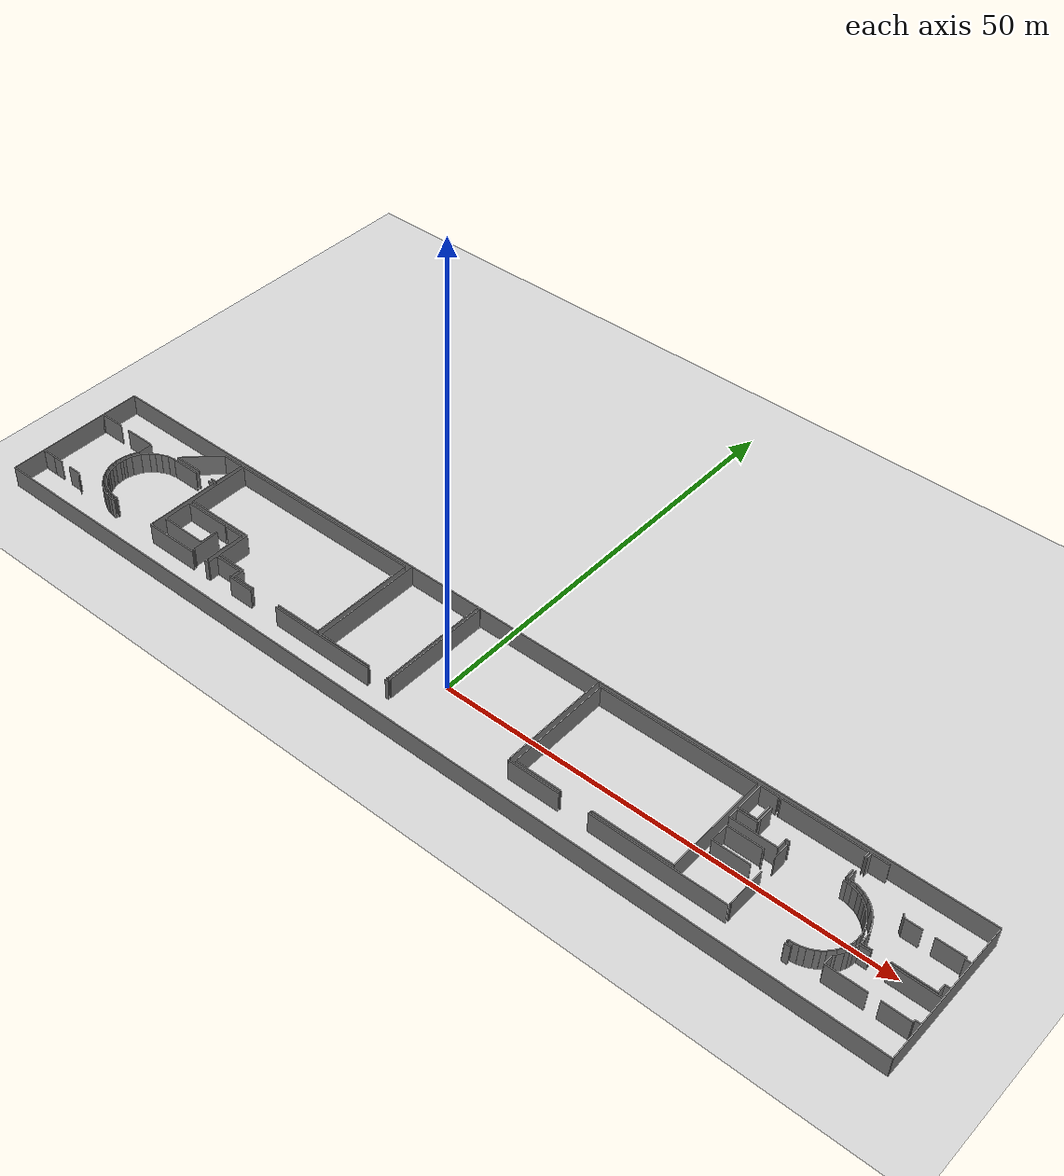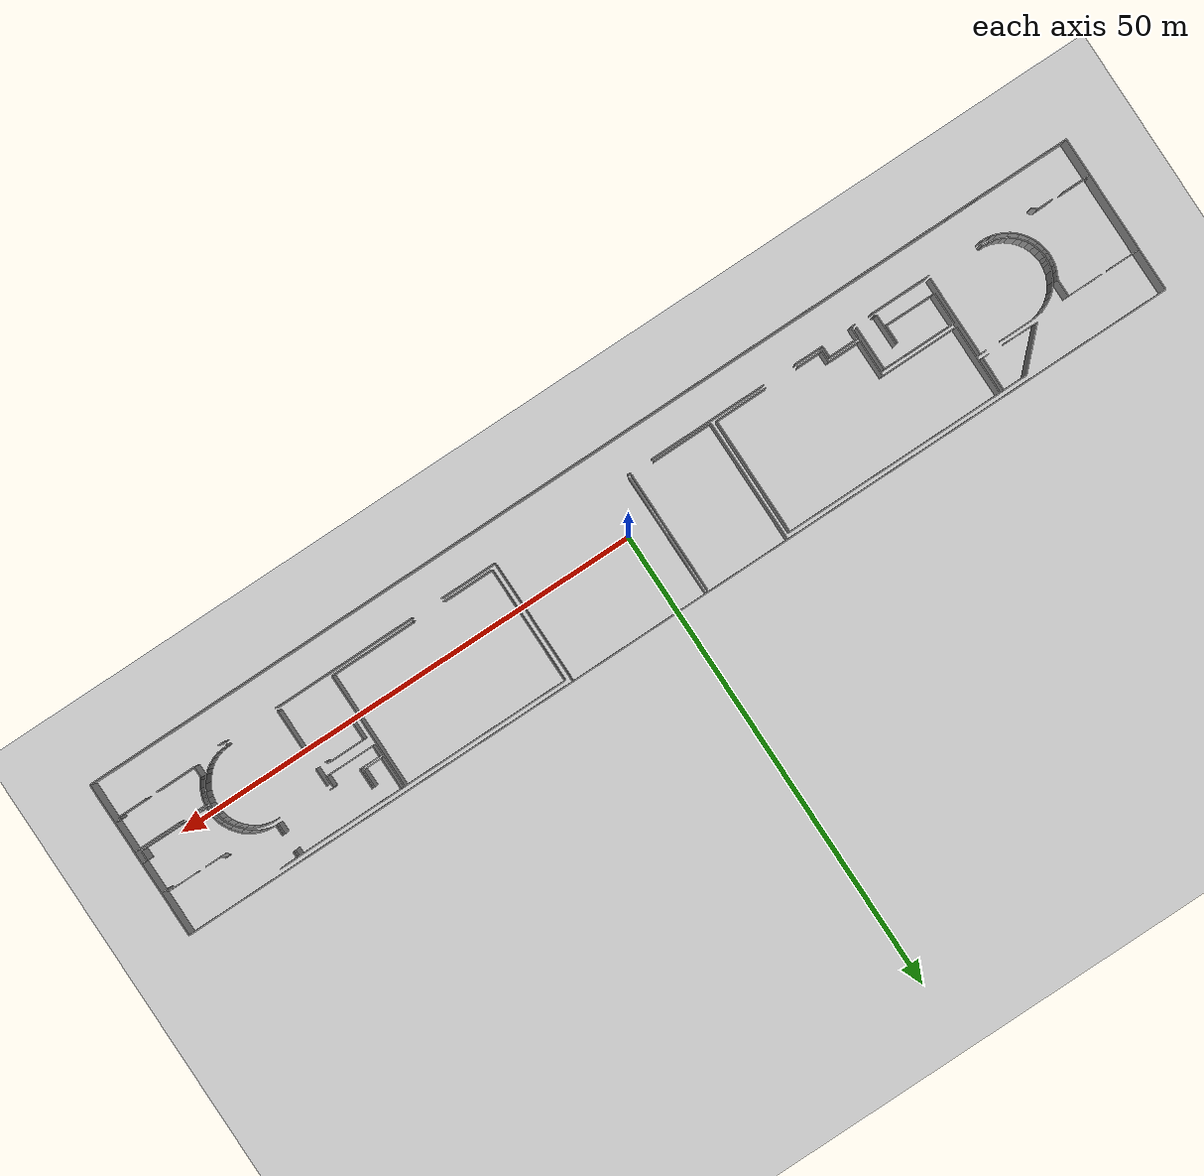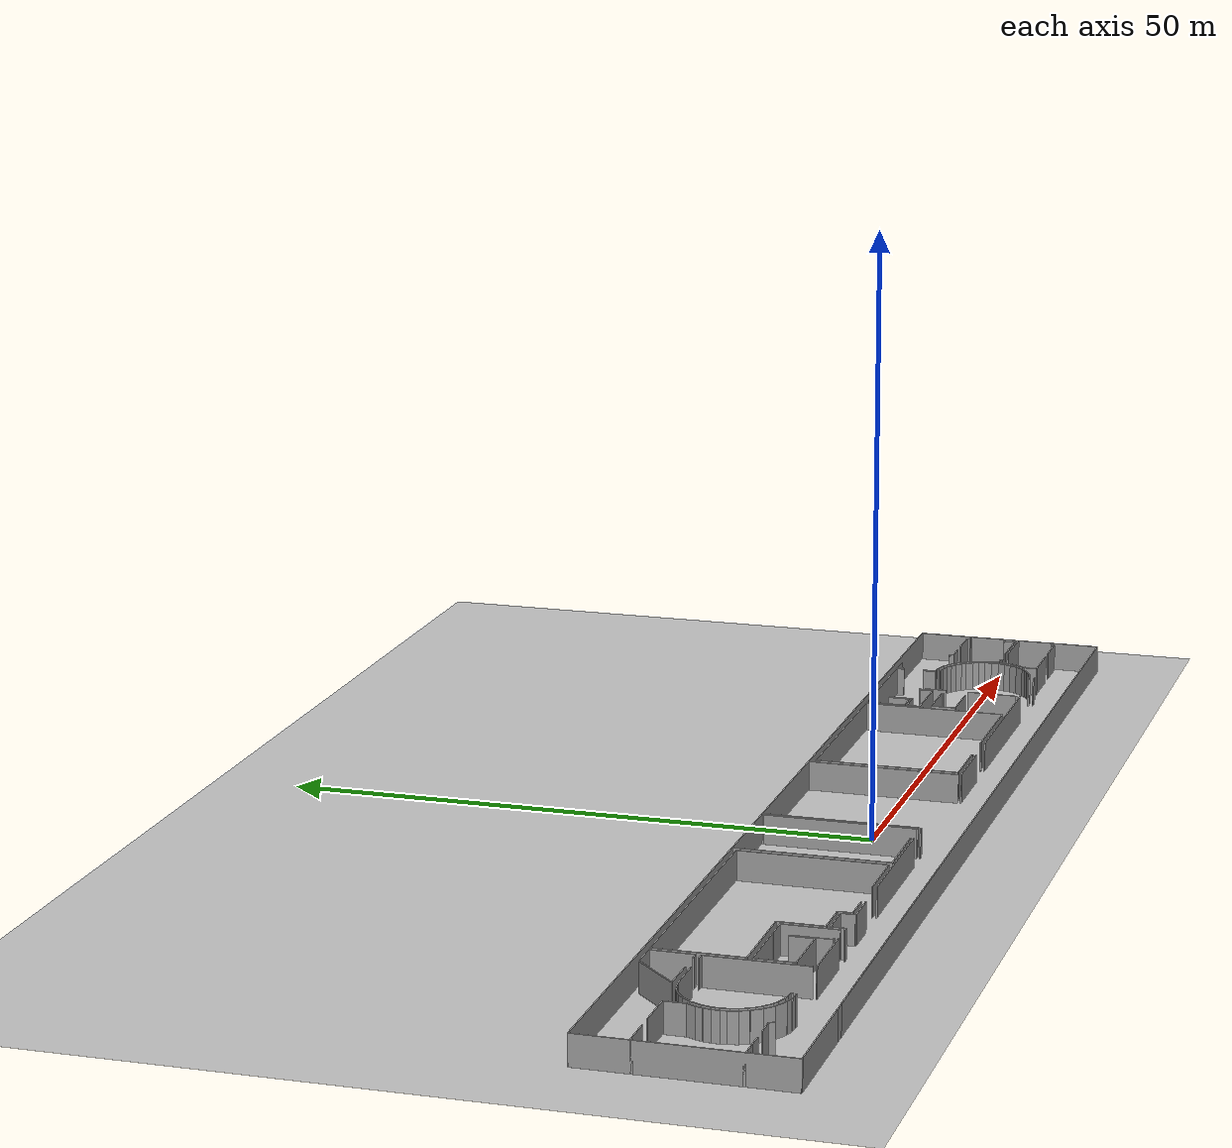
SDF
<sdf version="1.6">
  <world name="default">
    <light name="sun" type="directional">
      <cast_shadows>1</cast_shadows>
      <pose frame="">0 0 10 0 -0 0</pose>
      <diffuse>0.8 0.8 0.8 1</diffuse>
      <specular>0.1 0.1 0.1 1</specular>
      <attenuation>
        <range>1000</range>
        <constant>0.9</constant>
        <linear>0.01</linear>
        <quadratic>0.001</quadratic>
      </attenuation>
      <direction>-0.5 0.5 -1</direction>
    </light>
    <model name="ground_plane">
      <static>1</static>
      <link name="link">
        <collision name="collision">
          <geometry>
            <plane>
              <normal>0 0 1</normal>
              <size>100 100</size>
            </plane>
          </geometry>
          <surface>
            <friction>
              <ode>
                <mu>100</mu>
                <mu2>50</mu2>
              </ode>
              <torsional>
                <ode />
              </torsional>
            </friction>
            <contact>
              <ode />
            </contact>
            <bounce />
          </surface>
          <max_contacts>10</max_contacts>
        </collision>
        <visual name="visual">
          <cast_shadows>0</cast_shadows>
          <geometry>
            <plane>
              <normal>0 0 1</normal>
              <size>100 100</size>
            </plane>
          </geometry>
          <material>
            <script>
              <uri>file://media/materials/scripts/gazebo.material</uri>
              <name>Gazebo/Grey</name>
            </script>
          </material>
        </visual>
        <self_collide>0</self_collide>
        <kinematic>0</kinematic>
        <gravity>1</gravity>
      </link>
    </model>
    <gravity>0 0 -9.8</gravity>
    <magnetic_field>6e-06 2.3e-05 -4.2e-05</magnetic_field>
    <atmosphere type="adiabatic" />
    <physics default="0" name="default_physics" type="ode">
      <max_step_size>0.001</max_step_size>
      <real_time_factor>1</real_time_factor>
      <real_time_update_rate>1000</real_time_update_rate>
    </physics>
    <scene>
      <ambient>0.4 0.4 0.4 1</ambient>
      <background>0.7 0.7 0.7 1</background>
      <shadows>1</shadows>
    </scene>
    <spherical_coordinates>
      <surface_model>EARTH_WGS84</surface_model>
      <latitude_deg>0</latitude_deg>
      <longitude_deg>0</longitude_deg>
      <elevation>0</elevation>
      <heading_deg>0</heading_deg>
    </spherical_coordinates>
  <model name="50041175">
		<static>1</static>
		<link name="Wall_0">
			<collision name="Wall_0_Collision">
				<geometry>
					<box>
						<size>1.6562662837 0.1 2.5</size>
					</box>
				</geometry>
				<pose frame="">0.828133141848 0 1.25 0 0 0</pose>
			</collision>
			<visual name="Wall_0_Visual">
				<pose frame="">0.828133141848 0 1.25 0 0 0</pose>
				<geometry>
					<box>
						<size>1.6562662837 0.1 2.5</size>
					</box>
				</geometry>
				<material>
					<script>
						<uri>file://media/materials/scripts/gazebo.material</uri>
						<name>Gazebo/Grey</name>
					</script>
					<ambient>1 1 1 1</ambient>
				</material>
			</visual>
			<pose frame="">1.6562662837 -12.7340086169 0 0 0 3.14159265359</pose>
		</link>
		<link name="Wall_1">
			<collision name="Wall_1_Collision">
				<geometry>
					<box>
						<size>0.231689183178 0.1 2.5</size>
					</box>
				</geometry>
				<pose frame="">0.115844591589 0 1.25 0 0 0</pose>
			</collision>
			<visual name="Wall_1_Visual">
				<pose frame="">0.115844591589 0 1.25 0 0 0</pose>
				<geometry>
					<box>
						<size>0.231689183178 0.1 2.5</size>
					</box>
				</geometry>
				<material>
					<script>
						<uri>file://media/materials/scripts/gazebo.material</uri>
						<name>Gazebo/Grey</name>
					</script>
					<ambient>1 1 1 1</ambient>
				</material>
			</visual>
			<pose frame="">0.0 -12.7340086169 0 0 0 1.57079632679</pose>
		</link>
		<link name="Wall_2">
			<collision name="Wall_2_Collision">
				<geometry>
					<box>
						<size>0.238806349529 0.1 2.5</size>
					</box>
				</geometry>
				<pose frame="">0.119403174765 0 1.25 0 0 0</pose>
			</collision>
			<visual name="Wall_2_Visual">
				<pose frame="">0.119403174765 0 1.25 0 0 0</pose>
				<geometry>
					<box>
						<size>0.238806349529 0.1 2.5</size>
					</box>
				</geometry>
				<material>
					<script>
						<uri>file://media/materials/scripts/gazebo.material</uri>
						<name>Gazebo/Grey</name>
					</script>
					<ambient>1 1 1 1</ambient>
				</material>
			</visual>
			<pose frame="">0.0 -4.70190511292 0 0 0 1.57079632679</pose>
		</link>
		<link name="Wall_3">
			<collision name="Wall_3_Collision">
				<geometry>
					<box>
						<size>2.970146029 0.1 2.5</size>
					</box>
				</geometry>
				<pose frame="">1.4850730145 0 1.25 0 0 0</pose>
			</collision>
			<visual name="Wall_3_Visual">
				<pose frame="">1.4850730145 0 1.25 0 0 0</pose>
				<geometry>
					<box>
						<size>2.970146029 0.1 2.5</size>
					</box>
				</geometry>
				<material>
					<script>
						<uri>file://media/materials/scripts/gazebo.material</uri>
						<name>Gazebo/Grey</name>
					</script>
					<ambient>1 1 1 1</ambient>
				</material>
			</visual>
			<pose frame="">0.0 -4.46309876339 0 0 0 0.0</pose>
		</link>
		<link name="Wall_4">
			<collision name="Wall_4_Collision">
				<geometry>
					<box>
						<size>3.68122720283 0.1 2.5</size>
					</box>
				</geometry>
				<pose frame="">1.84061360141 0 1.25 0 0 0</pose>
			</collision>
			<visual name="Wall_4_Visual">
				<pose frame="">1.84061360141 0 1.25 0 0 0</pose>
				<geometry>
					<box>
						<size>3.68122720283 0.1 2.5</size>
					</box>
				</geometry>
				<material>
					<script>
						<uri>file://media/materials/scripts/gazebo.material</uri>
						<name>Gazebo/Grey</name>
					</script>
					<ambient>1 1 1 1</ambient>
				</material>
			</visual>
			<pose frame="">4.14422429241 -4.46309876339 0 0 0 0.0</pose>
		</link>
		<link name="Wall_5">
			<collision name="Wall_5_Collision">
				<geometry>
					<box>
						<size>1.7719202369 0.1 2.5</size>
					</box>
				</geometry>
				<pose frame="">0.88596011845 0 1.25 0 0 0</pose>
			</collision>
			<visual name="Wall_5_Visual">
				<pose frame="">0.88596011845 0 1.25 0 0 0</pose>
				<geometry>
					<box>
						<size>1.7719202369 0.1 2.5</size>
					</box>
				</geometry>
				<material>
					<script>
						<uri>file://media/materials/scripts/gazebo.material</uri>
						<name>Gazebo/Grey</name>
					</script>
					<ambient>1 1 1 1</ambient>
				</material>
			</visual>
			<pose frame="">7.82545149524 -4.46309876339 0 0 0 -1.57079632679</pose>
		</link>
		<link name="Wall_6">
			<collision name="Wall_6_Collision">
				<geometry>
					<box>
						<size>0.846830648124 0.1 2.5</size>
					</box>
				</geometry>
				<pose frame="">0.423415324062 0 1.25 0 0 0</pose>
			</collision>
			<visual name="Wall_6_Visual">
				<pose frame="">0.423415324062 0 1.25 0 0 0</pose>
				<geometry>
					<box>
						<size>0.846830648124 0.1 2.5</size>
					</box>
				</geometry>
				<material>
					<script>
						<uri>file://media/materials/scripts/gazebo.material</uri>
						<name>Gazebo/Grey</name>
					</script>
					<ambient>1 1 1 1</ambient>
				</material>
			</visual>
			<pose frame="">7.82545149524 -6.23501900029 0 0 0 -2.01377018992</pose>
		</link>
		<link name="Wall_7">
			<collision name="Wall_7_Collision">
				<geometry>
					<box>
						<size>0.615985382137 0.1 2.5</size>
					</box>
				</geometry>
				<pose frame="">0.307992691069 0 1.25 0 0 0</pose>
			</collision>
			<visual name="Wall_7_Visual">
				<pose frame="">0.307992691069 0 1.25 0 0 0</pose>
				<geometry>
					<box>
						<size>0.615985382137 0.1 2.5</size>
					</box>
				</geometry>
				<material>
					<script>
						<uri>file://media/materials/scripts/gazebo.material</uri>
						<name>Gazebo/Grey</name>
					</script>
					<ambient>1 1 1 1</ambient>
				</material>
			</visual>
			<pose frame="">7.46247601134 -7.00011438303 0 0 0 -1.87029642608</pose>
		</link>
		<link name="Wall_8">
			<collision name="Wall_8_Collision">
				<geometry>
					<box>
						<size>0.661872701431 0.1 2.5</size>
					</box>
				</geometry>
				<pose frame="">0.330936350716 0 1.25 0 0 0</pose>
			</collision>
			<visual name="Wall_8_Visual">
				<pose frame="">0.330936350716 0 1.25 0 0 0</pose>
				<geometry>
					<box>
						<size>0.661872701431 0.1 2.5</size>
					</box>
				</geometry>
				<material>
					<script>
						<uri>file://media/materials/scripts/gazebo.material</uri>
						<name>Gazebo/Grey</name>
					</script>
					<ambient>1 1 1 1</ambient>
				</material>
			</visual>
			<pose frame="">7.28073408487 -7.58867862181 0 0 0 -1.72502234225</pose>
		</link>
		<link name="Wall_9">
			<collision name="Wall_9_Collision">
				<geometry>
					<box>
						<size>0.646685976722 0.1 2.5</size>
					</box>
				</geometry>
				<pose frame="">0.323342988361 0 1.25 0 0 0</pose>
			</collision>
			<visual name="Wall_9_Visual">
				<pose frame="">0.323342988361 0 1.25 0 0 0</pose>
				<geometry>
					<box>
						<size>0.646685976722 0.1 2.5</size>
					</box>
				</geometry>
				<material>
					<script>
						<uri>file://media/materials/scripts/gazebo.material</uri>
						<name>Gazebo/Grey</name>
					</script>
					<ambient>1 1 1 1</ambient>
				</material>
			</visual>
			<pose frame="">7.17906027986 -8.24269537257 0 0 0 -1.58199868835</pose>
		</link>
		<link name="Wall_10">
			<collision name="Wall_10_Collision">
				<geometry>
					<box>
						<size>0.439904652623 0.1 2.5</size>
					</box>
				</geometry>
				<pose frame="">0.219952326311 0 1.25 0 0 0</pose>
			</collision>
			<visual name="Wall_10_Visual">
				<pose frame="">0.219952326311 0 1.25 0 0 0</pose>
				<geometry>
					<box>
						<size>0.439904652623 0.1 2.5</size>
					</box>
				</geometry>
				<material>
					<script>
						<uri>file://media/materials/scripts/gazebo.material</uri>
						<name>Gazebo/Grey</name>
					</script>
					<ambient>1 1 1 1</ambient>
				</material>
			</visual>
			<pose frame="">7.17181602125 -8.88934077247 0 0 0 -1.43837843584</pose>
		</link>
		<link name="Wall_11">
			<collision name="Wall_11_Collision">
				<geometry>
					<box>
						<size>0.838824392635 0.1 2.5</size>
					</box>
				</geometry>
				<pose frame="">0.419412196318 0 1.25 0 0 0</pose>
			</collision>
			<visual name="Wall_11_Visual">
				<pose frame="">0.419412196318 0 1.25 0 0 0</pose>
				<geometry>
					<box>
						<size>0.838824392635 0.1 2.5</size>
					</box>
				</geometry>
				<material>
					<script>
						<uri>file://media/materials/scripts/gazebo.material</uri>
						<name>Gazebo/Grey</name>
					</script>
					<ambient>1 1 1 1</ambient>
				</material>
			</visual>
			<pose frame="">7.22989718236 -9.32539430373 0 0 0 -1.32578091653</pose>
		</link>
		<link name="Wall_12">
			<collision name="Wall_12_Collision">
				<geometry>
					<box>
						<size>0.809514762314 0.1 2.5</size>
					</box>
				</geometry>
				<pose frame="">0.404757381157 0 1.25 0 0 0</pose>
			</collision>
			<visual name="Wall_12_Visual">
				<pose frame="">0.404757381157 0 1.25 0 0 0</pose>
				<geometry>
					<box>
						<size>0.809514762314 0.1 2.5</size>
					</box>
				</geometry>
				<material>
					<script>
						<uri>file://media/materials/scripts/gazebo.material</uri>
						<name>Gazebo/Grey</name>
					</script>
					<ambient>1 1 1 1</ambient>
				</material>
			</visual>
			<pose frame="">7.43337188465 -10.1391660206 0 0 0 -1.13530731927</pose>
		</link>
		<link name="Wall_13">
			<collision name="Wall_13_Collision">
				<geometry>
					<box>
						<size>0.988325124962 0.1 2.5</size>
					</box>
				</geometry>
				<pose frame="">0.494162562481 0 1.25 0 0 0</pose>
			</collision>
			<visual name="Wall_13_Visual">
				<pose frame="">0.494162562481 0 1.25 0 0 0</pose>
				<geometry>
					<box>
						<size>0.988325124962 0.1 2.5</size>
					</box>
				</geometry>
				<material>
					<script>
						<uri>file://media/materials/scripts/gazebo.material</uri>
						<name>Gazebo/Grey</name>
					</script>
					<ambient>1 1 1 1</ambient>
				</material>
			</visual>
			<pose frame="">7.77486877725 -10.8731238006 0 0 0 -0.941981131605</pose>
		</link>
		<link name="Wall_14">
			<collision name="Wall_14_Collision">
				<geometry>
					<box>
						<size>0.98253685153 0.1 2.5</size>
					</box>
				</geometry>
				<pose frame="">0.491268425765 0 1.25 0 0 0</pose>
			</collision>
			<visual name="Wall_14_Visual">
				<pose frame="">0.491268425765 0 1.25 0 0 0</pose>
				<geometry>
					<box>
						<size>0.98253685153 0.1 2.5</size>
					</box>
				</geometry>
				<material>
					<script>
						<uri>file://media/materials/scripts/gazebo.material</uri>
						<name>Gazebo/Grey</name>
					</script>
					<ambient>1 1 1 1</ambient>
				</material>
			</visual>
			<pose frame="">8.35618875742 -11.6724070002 0 0 0 -0.738276218378</pose>
		</link>
		<link name="Wall_15">
			<collision name="Wall_15_Collision">
				<geometry>
					<box>
						<size>1.1946351515 0.1 2.5</size>
					</box>
				</geometry>
				<pose frame="">0.597317575752 0 1.25 0 0 0</pose>
			</collision>
			<visual name="Wall_15_Visual">
				<pose frame="">0.597317575752 0 1.25 0 0 0</pose>
				<geometry>
					<box>
						<size>1.1946351515 0.1 2.5</size>
					</box>
				</geometry>
				<material>
					<script>
						<uri>file://media/materials/scripts/gazebo.material</uri>
						<name>Gazebo/Grey</name>
					</script>
					<ambient>1 1 1 1</ambient>
				</material>
			</visual>
			<pose frame="">9.08290227876 -12.3336680096 0 0 0 -0.475494606704</pose>
		</link>
		<link name="Wall_16">
			<collision name="Wall_16_Collision">
				<geometry>
					<box>
						<size>0.620881470011 0.1 2.5</size>
					</box>
				</geometry>
				<pose frame="">0.310440735005 0 1.25 0 0 0</pose>
			</collision>
			<visual name="Wall_16_Visual">
				<pose frame="">0.310440735005 0 1.25 0 0 0</pose>
				<geometry>
					<box>
						<size>0.620881470011 0.1 2.5</size>
					</box>
				</geometry>
				<material>
					<script>
						<uri>file://media/materials/scripts/gazebo.material</uri>
						<name>Gazebo/Grey</name>
					</script>
					<ambient>1 1 1 1</ambient>
				</material>
			</visual>
			<pose frame="">10.1450122644 -12.8805459883 0 0 0 -0.282967135303</pose>
		</link>
		<link name="Wall_17">
			<collision name="Wall_17_Collision">
				<geometry>
					<box>
						<size>1.03326004347 0.1 2.5</size>
					</box>
				</geometry>
				<pose frame="">0.516630021733 0 1.25 0 0 0</pose>
			</collision>
			<visual name="Wall_17_Visual">
				<pose frame="">0.516630021733 0 1.25 0 0 0</pose>
				<geometry>
					<box>
						<size>1.03326004347 0.1 2.5</size>
					</box>
				</geometry>
				<material>
					<script>
						<uri>file://media/materials/scripts/gazebo.material</uri>
						<name>Gazebo/Grey</name>
					</script>
					<ambient>1 1 1 1</ambient>
				</material>
			</visual>
			<pose frame="">10.7412020386 -16.6847984952 0 0 0 3.14159265359</pose>
		</link>
		<link name="Wall_18">
			<collision name="Wall_18_Collision">
				<geometry>
					<box>
						<size>0.562572519334 0.1 2.5</size>
					</box>
				</geometry>
				<pose frame="">0.281286259667 0 1.25 0 0 0</pose>
			</collision>
			<visual name="Wall_18_Visual">
				<pose frame="">0.281286259667 0 1.25 0 0 0</pose>
				<geometry>
					<box>
						<size>0.562572519334 0.1 2.5</size>
					</box>
				</geometry>
				<material>
					<script>
						<uri>file://media/materials/scripts/gazebo.material</uri>
						<name>Gazebo/Grey</name>
					</script>
					<ambient>1 1 1 1</ambient>
				</material>
			</visual>
			<pose frame="">6.16905811929 -13.1409580214 0 0 0 2.35683346774</pose>
		</link>
		<link name="Wall_19">
			<collision name="Wall_19_Collision">
				<geometry>
					<box>
						<size>1.62500158865 0.1 2.5</size>
					</box>
				</geometry>
				<pose frame="">0.812500794327 0 1.25 0 0 0</pose>
			</collision>
			<visual name="Wall_19_Visual">
				<pose frame="">0.812500794327 0 1.25 0 0 0</pose>
				<geometry>
					<box>
						<size>1.62500158865 0.1 2.5</size>
					</box>
				</geometry>
				<material>
					<script>
						<uri>file://media/materials/scripts/gazebo.material</uri>
						<name>Gazebo/Grey</name>
					</script>
					<ambient>1 1 1 1</ambient>
				</material>
			</visual>
			<pose frame="">5.77100517265 -12.7434134438 0 0 0 3.14159265359</pose>
		</link>
		<link name="Wall_20">
			<collision name="Wall_20_Collision">
				<geometry>
					<box>
						<size>1.30577971029 0.1 2.5</size>
					</box>
				</geometry>
				<pose frame="">0.652889855147 0 1.25 0 0 0</pose>
			</collision>
			<visual name="Wall_20_Visual">
				<pose frame="">0.652889855147 0 1.25 0 0 0</pose>
				<geometry>
					<box>
						<size>1.30577971029 0.1 2.5</size>
					</box>
				</geometry>
				<material>
					<script>
						<uri>file://media/materials/scripts/gazebo.material</uri>
						<name>Gazebo/Grey</name>
					</script>
					<ambient>1 1 1 1</ambient>
				</material>
			</visual>
			<pose frame="">2.9620121246 -12.7434134438 0 0 0 3.13439013068</pose>
		</link>
		<link name="Wall_21">
			<collision name="Wall_21_Collision">
				<geometry>
					<box>
						<size>0.36281847588 0.1 2.5</size>
					</box>
				</geometry>
				<pose frame="">0.18140923794 0 1.25 0 0 0</pose>
			</collision>
			<visual name="Wall_21_Visual">
				<pose frame="">0.18140923794 0 1.25 0 0 0</pose>
				<geometry>
					<box>
						<size>0.36281847588 0.1 2.5</size>
					</box>
				</geometry>
				<material>
					<script>
						<uri>file://media/materials/scripts/gazebo.material</uri>
						<name>Gazebo/Grey</name>
					</script>
					<ambient>1 1 1 1</ambient>
				</material>
			</visual>
			<pose frame="">7.64993708933 -8.35364691229 0 0 0 1.47255674269</pose>
		</link>
		<link name="Wall_22">
			<collision name="Wall_22_Collision">
				<geometry>
					<box>
						<size>0.719627656 0.1 2.5</size>
					</box>
				</geometry>
				<pose frame="">0.359813828 0 1.25 0 0 0</pose>
			</collision>
			<visual name="Wall_22_Visual">
				<pose frame="">0.359813828 0 1.25 0 0 0</pose>
				<geometry>
					<box>
						<size>0.719627656 0.1 2.5</size>
					</box>
				</geometry>
				<material>
					<script>
						<uri>file://media/materials/scripts/gazebo.material</uri>
						<name>Gazebo/Grey</name>
					</script>
					<ambient>1 1 1 1</ambient>
				</material>
			</visual>
			<pose frame="">7.68552292109 -7.99257781223 0 0 0 1.34856438238</pose>
		</link>
		<link name="Wall_23">
			<collision name="Wall_23_Collision">
				<geometry>
					<box>
						<size>1.03548684681 0.1 2.5</size>
					</box>
				</geometry>
				<pose frame="">0.517743423406 0 1.25 0 0 0</pose>
			</collision>
			<visual name="Wall_23_Visual">
				<pose frame="">0.517743423406 0 1.25 0 0 0</pose>
				<geometry>
					<box>
						<size>1.03548684681 0.1 2.5</size>
					</box>
				</geometry>
				<material>
					<script>
						<uri>file://media/materials/scripts/gazebo.material</uri>
						<name>Gazebo/Grey</name>
					</script>
					<ambient>1 1 1 1</ambient>
				</material>
			</visual>
			<pose frame="">7.84413405691 -7.29064728086 0 0 0 1.13152208163</pose>
		</link>
		<link name="Wall_24">
			<collision name="Wall_24_Collision">
				<geometry>
					<box>
						<size>0.887161138428 0.1 2.5</size>
					</box>
				</geometry>
				<pose frame="">0.443580569214 0 1.25 0 0 0</pose>
			</collision>
			<visual name="Wall_24_Visual">
				<pose frame="">0.443580569214 0 1.25 0 0 0</pose>
				<geometry>
					<box>
						<size>0.887161138428 0.1 2.5</size>
					</box>
				</geometry>
				<material>
					<script>
						<uri>file://media/materials/scripts/gazebo.material</uri>
						<name>Gazebo/Grey</name>
					</script>
					<ambient>1 1 1 1</ambient>
				</material>
			</visual>
			<pose frame="">8.28450872488 -6.35346898313 0 0 0 0.8775070857</pose>
		</link>
		<link name="Wall_25">
			<collision name="Wall_25_Collision">
				<geometry>
					<box>
						<size>0.648414988856 0.1 2.5</size>
					</box>
				</geometry>
				<pose frame="">0.324207494428 0 1.25 0 0 0</pose>
			</collision>
			<visual name="Wall_25_Visual">
				<pose frame="">0.324207494428 0 1.25 0 0 0</pose>
				<geometry>
					<box>
						<size>0.648414988856 0.1 2.5</size>
					</box>
				</geometry>
				<material>
					<script>
						<uri>file://media/materials/scripts/gazebo.material</uri>
						<name>Gazebo/Grey</name>
					</script>
					<ambient>1 1 1 1</ambient>
				</material>
			</visual>
			<pose frame="">8.8514672801 -5.67111065923 0 0 0 0.690873512645</pose>
		</link>
		<link name="Wall_26">
			<collision name="Wall_26_Collision">
				<geometry>
					<box>
						<size>0.698898147814 0.1 2.5</size>
					</box>
				</geometry>
				<pose frame="">0.349449073907 0 1.25 0 0 0</pose>
			</collision>
			<visual name="Wall_26_Visual">
				<pose frame="">0.349449073907 0 1.25 0 0 0</pose>
				<geometry>
					<box>
						<size>0.698898147814 0.1 2.5</size>
					</box>
				</geometry>
				<material>
					<script>
						<uri>file://media/materials/scripts/gazebo.material</uri>
						<name>Gazebo/Grey</name>
					</script>
					<ambient>1 1 1 1</ambient>
				</material>
			</visual>
			<pose frame="">9.35119403175 -5.2579337341 0 0 0 0.531687187303</pose>
		</link>
		<link name="Wall_27">
			<collision name="Wall_27_Collision">
				<geometry>
					<box>
						<size>0.801340088225 0.1 2.5</size>
					</box>
				</geometry>
				<pose frame="">0.400670044113 0 1.25 0 0 0</pose>
			</collision>
			<visual name="Wall_27_Visual">
				<pose frame="">0.400670044113 0 1.25 0 0 0</pose>
				<geometry>
					<box>
						<size>0.801340088225 0.1 2.5</size>
					</box>
				</geometry>
				<material>
					<script>
						<uri>file://media/materials/scripts/gazebo.material</uri>
						<name>Gazebo/Grey</name>
					</script>
					<ambient>1 1 1 1</ambient>
				</material>
			</visual>
			<pose frame="">9.95361132646 -4.90360052362 0 0 0 0.385689814226</pose>
		</link>
		<link name="Wall_28">
			<collision name="Wall_28_Collision">
				<geometry>
					<box>
						<size>0.866344135107 0.1 2.5</size>
					</box>
				</geometry>
				<pose frame="">0.433172067554 0 1.25 0 0 0</pose>
			</collision>
			<visual name="Wall_28_Visual">
				<pose frame="">0.433172067554 0 1.25 0 0 0</pose>
				<geometry>
					<box>
						<size>0.866344135107 0.1 2.5</size>
					</box>
				</geometry>
				<material>
					<script>
						<uri>file://media/materials/scripts/gazebo.material</uri>
						<name>Gazebo/Grey</name>
					</script>
					<ambient>1 1 1 1</ambient>
				</material>
			</visual>
			<pose frame="">10.6960842876 -4.60213769175 0 0 0 0.143079602133</pose>
		</link>
		<link name="Wall_29">
			<collision name="Wall_29_Collision">
				<geometry>
					<box>
						<size>3.39959076293 0.1 2.5</size>
					</box>
				</geometry>
				<pose frame="">1.69979538147 0 1.25 0 0 0</pose>
			</collision>
			<visual name="Wall_29_Visual">
				<pose frame="">1.69979538147 0 1.25 0 0 0</pose>
				<geometry>
					<box>
						<size>3.39959076293 0.1 2.5</size>
					</box>
				</geometry>
				<material>
					<script>
						<uri>file://media/materials/scripts/gazebo.material</uri>
						<name>Gazebo/Grey</name>
					</script>
					<ambient>1 1 1 1</ambient>
				</material>
			</visual>
			<pose frame="">11.5535757406 -4.47860401866 0 0 0 0.0</pose>
		</link>
		<link name="Wall_30">
			<collision name="Wall_30_Collision">
				<geometry>
					<box>
						<size>0.673716050481 0.1 2.5</size>
					</box>
				</geometry>
				<pose frame="">0.336858025241 0 1.25 0 0 0</pose>
			</collision>
			<visual name="Wall_30_Visual">
				<pose frame="">0.336858025241 0 1.25 0 0 0</pose>
				<geometry>
					<box>
						<size>0.673716050481 0.1 2.5</size>
					</box>
				</geometry>
				<material>
					<script>
						<uri>file://media/materials/scripts/gazebo.material</uri>
						<name>Gazebo/Grey</name>
					</script>
					<ambient>1 1 1 1</ambient>
				</material>
			</visual>
			<pose frame="">16.9125478185 -4.47860401866 0 0 0 0.0</pose>
		</link>
		<link name="Wall_31">
			<collision name="Wall_31_Collision">
				<geometry>
					<box>
						<size>8.4236747455 0.1 2.5</size>
					</box>
				</geometry>
				<pose frame="">4.21183737275 0 1.25 0 0 0</pose>
			</collision>
			<visual name="Wall_31_Visual">
				<pose frame="">4.21183737275 0 1.25 0 0 0</pose>
				<geometry>
					<box>
						<size>8.4236747455 0.1 2.5</size>
					</box>
				</geometry>
				<material>
					<script>
						<uri>file://media/materials/scripts/gazebo.material</uri>
						<name>Gazebo/Grey</name>
					</script>
					<ambient>1 1 1 1</ambient>
				</material>
			</visual>
			<pose frame="">17.5862638689 -4.47860401866 0 0 0 -1.57079632679</pose>
		</link>
		<link name="Wall_32">
			<collision name="Wall_32_Collision">
				<geometry>
					<box>
						<size>0.180216819389 0.1 2.5</size>
					</box>
				</geometry>
				<pose frame="">0.0901084096946 0 1.25 0 0 0</pose>
			</collision>
			<visual name="Wall_32_Visual">
				<pose frame="">0.0901084096946 0 1.25 0 0 0</pose>
				<geometry>
					<box>
						<size>0.180216819389 0.1 2.5</size>
					</box>
				</geometry>
				<material>
					<script>
						<uri>file://media/materials/scripts/gazebo.material</uri>
						<name>Gazebo/Grey</name>
					</script>
					<ambient>1 1 1 1</ambient>
				</material>
			</visual>
			<pose frame="">11.9002834157 -12.9022787642 0 0 0 1.57079632679</pose>
		</link>
		<link name="Wall_33">
			<collision name="Wall_33_Collision">
				<geometry>
					<box>
						<size>0.659679686485 0.1 2.5</size>
					</box>
				</geometry>
				<pose frame="">0.329839843242 0 1.25 0 0 0</pose>
			</collision>
			<visual name="Wall_33_Visual">
				<pose frame="">0.329839843242 0 1.25 0 0 0</pose>
				<geometry>
					<box>
						<size>0.659679686485 0.1 2.5</size>
					</box>
				</geometry>
				<material>
					<script>
						<uri>file://media/materials/scripts/gazebo.material</uri>
						<name>Gazebo/Grey</name>
					</script>
					<ambient>1 1 1 1</ambient>
				</material>
			</visual>
			<pose frame="">11.9002834157 -12.7220619448 0 0 0 3.08762234943</pose>
		</link>
		<link name="Wall_34">
			<collision name="Wall_34_Collision">
				<geometry>
					<box>
						<size>0.57892062884 0.1 2.5</size>
					</box>
				</geometry>
				<pose frame="">0.28946031442 0 1.25 0 0 0</pose>
			</collision>
			<visual name="Wall_34_Visual">
				<pose frame="">0.28946031442 0 1.25 0 0 0</pose>
				<geometry>
					<box>
						<size>0.57892062884 0.1 2.5</size>
					</box>
				</geometry>
				<material>
					<script>
						<uri>file://media/materials/scripts/gazebo.material</uri>
						<name>Gazebo/Grey</name>
					</script>
					<ambient>1 1 1 1</ambient>
				</material>
			</visual>
			<pose frame="">11.2415642515 -12.686476113 0 0 0 2.95612333128</pose>
		</link>
		<link name="Wall_35">
			<collision name="Wall_35_Collision">
				<geometry>
					<box>
						<size>0.75556586854 0.1 2.5</size>
					</box>
				</geometry>
				<pose frame="">0.37778293427 0 1.25 0 0 0</pose>
			</collision>
			<visual name="Wall_35_Visual">
				<pose frame="">0.37778293427 0 1.25 0 0 0</pose>
				<geometry>
					<box>
						<size>0.75556586854 0.1 2.5</size>
					</box>
				</geometry>
				<material>
					<script>
						<uri>file://media/materials/scripts/gazebo.material</uri>
						<name>Gazebo/Grey</name>
					</script>
					<ambient>1 1 1 1</ambient>
				</material>
			</visual>
			<pose frame="">10.6725722202 -12.5797186177 0 0 0 2.79973414787</pose>
		</link>
		<link name="Wall_36">
			<collision name="Wall_36_Collision">
				<geometry>
					<box>
						<size>0.556449449577 0.1 2.5</size>
					</box>
				</geometry>
				<pose frame="">0.278224724788 0 1.25 0 0 0</pose>
			</collision>
			<visual name="Wall_36_Visual">
				<pose frame="">0.278224724788 0 1.25 0 0 0</pose>
				<geometry>
					<box>
						<size>0.556449449577 0.1 2.5</size>
					</box>
				</geometry>
				<material>
					<script>
						<uri>file://media/materials/scripts/gazebo.material</uri>
						<name>Gazebo/Grey</name>
					</script>
					<ambient>1 1 1 1</ambient>
				</material>
			</visual>
			<pose frame="">9.96072849281 -12.326423751 0 0 0 2.62040682433</pose>
		</link>
		<link name="Wall_37">
			<collision name="Wall_37_Collision">
				<geometry>
					<box>
						<size>0.796480954315 0.1 2.5</size>
					</box>
				</geometry>
				<pose frame="">0.398240477157 0 1.25 0 0 0</pose>
			</collision>
			<visual name="Wall_37_Visual">
				<pose frame="">0.398240477157 0 1.25 0 0 0</pose>
				<geometry>
					<box>
						<size>0.796480954315 0.1 2.5</size>
					</box>
				</geometry>
				<material>
					<script>
						<uri>file://media/materials/scripts/gazebo.material</uri>
						<name>Gazebo/Grey</name>
					</script>
					<ambient>1 1 1 1</ambient>
				</material>
			</visual>
			<pose frame="">9.47815919576 -12.0493626323 0 0 0 2.4368432702</pose>
		</link>
		<link name="Wall_38">
			<collision name="Wall_38_Collision">
				<geometry>
					<box>
						<size>0.595609380929 0.1 2.5</size>
					</box>
				</geometry>
				<pose frame="">0.297804690464 0 1.25 0 0 0</pose>
			</collision>
			<visual name="Wall_38_Visual">
				<pose frame="">0.297804690464 0 1.25 0 0 0</pose>
				<geometry>
					<box>
						<size>0.595609380929 0.1 2.5</size>
					</box>
				</geometry>
				<material>
					<script>
						<uri>file://media/materials/scripts/gazebo.material</uri>
						<name>Gazebo/Grey</name>
					</script>
					<ambient>1 1 1 1</ambient>
				</material>
			</visual>
			<pose frame="">8.87142076433 -11.5333680719 0 0 0 2.29958283771</pose>
		</link>
		<link name="Wall_39">
			<collision name="Wall_39_Collision">
				<geometry>
					<box>
						<size>0.598957380622 0.1 2.5</size>
					</box>
				</geometry>
				<pose frame="">0.299478690311 0 1.25 0 0 0</pose>
			</collision>
			<visual name="Wall_39_Visual">
				<pose frame="">0.299478690311 0 1.25 0 0 0</pose>
				<geometry>
					<box>
						<size>0.598957380622 0.1 2.5</size>
					</box>
				</geometry>
				<material>
					<script>
						<uri>file://media/materials/scripts/gazebo.material</uri>
						<name>Gazebo/Grey</name>
					</script>
					<ambient>1 1 1 1</ambient>
				</material>
			</visual>
			<pose frame="">8.47476583252 -11.089053544 0 0 0 2.16309504327</pose>
		</link>
		<link name="Wall_40">
			<collision name="Wall_40_Collision">
				<geometry>
					<box>
						<size>0.629272585491 0.1 2.5</size>
					</box>
				</geometry>
				<pose frame="">0.314636292745 0 1.25 0 0 0</pose>
			</collision>
			<visual name="Wall_40_Visual">
				<pose frame="">0.314636292745 0 1.25 0 0 0</pose>
				<geometry>
					<box>
						<size>0.629272585491 0.1 2.5</size>
					</box>
				</geometry>
				<material>
					<script>
						<uri>file://media/materials/scripts/gazebo.material</uri>
						<name>Gazebo/Grey</name>
					</script>
					<ambient>1 1 1 1</ambient>
				</material>
			</visual>
			<pose frame="">8.14038610627 -10.592122822 0 0 0 1.97669585645</pose>
		</link>
		<link name="Wall_41">
			<collision name="Wall_41_Collision">
				<geometry>
					<box>
						<size>0.627945076952 0.1 2.5</size>
					</box>
				</geometry>
				<pose frame="">0.313972538476 0 1.25 0 0 0</pose>
			</collision>
			<visual name="Wall_41_Visual">
				<pose frame="">0.313972538476 0 1.25 0 0 0</pose>
				<geometry>
					<box>
						<size>0.627945076952 0.1 2.5</size>
					</box>
				</geometry>
				<material>
					<script>
						<uri>file://media/materials/scripts/gazebo.material</uri>
						<name>Gazebo/Grey</name>
					</script>
					<ambient>1 1 1 1</ambient>
				</material>
			</visual>
			<pose frame="">7.89192074527 -10.0139801482 0 0 0 1.84965200465</pose>
		</link>
		<link name="Wall_42">
			<collision name="Wall_42_Collision">
				<geometry>
					<box>
						<size>0.695092077512 0.1 2.5</size>
					</box>
				</geometry>
				<pose frame="">0.347546038756 0 1.25 0 0 0</pose>
			</collision>
			<visual name="Wall_42_Visual">
				<pose frame="">0.347546038756 0 1.25 0 0 0</pose>
				<geometry>
					<box>
						<size>0.695092077512 0.1 2.5</size>
					</box>
				</geometry>
				<material>
					<script>
						<uri>file://media/materials/scripts/gazebo.material</uri>
						<name>Gazebo/Grey</name>
					</script>
					<ambient>1 1 1 1</ambient>
				</material>
			</visual>
			<pose frame="">7.71907527674 -9.41029193091 0 0 0 1.69655740741</pose>
		</link>
		<link name="Wall_43">
			<collision name="Wall_43_Collision">
				<geometry>
					<box>
						<size>0.367485846985 0.1 2.5</size>
					</box>
				</geometry>
				<pose frame="">0.183742923492 0 1.25 0 0 0</pose>
			</collision>
			<visual name="Wall_43_Visual">
				<pose frame="">0.183742923492 0 1.25 0 0 0</pose>
				<geometry>
					<box>
						<size>0.367485846985 0.1 2.5</size>
					</box>
				</geometry>
				<material>
					<script>
						<uri>file://media/materials/scripts/gazebo.material</uri>
						<name>Gazebo/Grey</name>
					</script>
					<ambient>1 1 1 1</ambient>
				</material>
			</visual>
			<pose frame="">7.63188998894 -8.7206893484 0 0 0 1.52166691779</pose>
		</link>
		<link name="Wall_44">
			<collision name="Wall_44_Collision">
				<geometry>
					<box>
						<size>3.33553626578 0.1 2.5</size>
					</box>
				</geometry>
				<pose frame="">1.66776813289 0 1.25 0 0 0</pose>
			</collision>
			<visual name="Wall_44_Visual">
				<pose frame="">1.66776813289 0 1.25 0 0 0</pose>
				<geometry>
					<box>
						<size>3.33553626578 0.1 2.5</size>
					</box>
				</geometry>
				<material>
					<script>
						<uri>file://media/materials/scripts/gazebo.material</uri>
						<name>Gazebo/Grey</name>
					</script>
					<ambient>1 1 1 1</ambient>
				</material>
			</visual>
			<pose frame="">23.5733258773 -12.8295819936 0 0 0 1.57079632679</pose>
		</link>
		<link name="Wall_45">
			<collision name="Wall_45_Collision">
				<geometry>
					<box>
						<size>2.18306368593 0.1 2.5</size>
					</box>
				</geometry>
				<pose frame="">1.09153184296 0 1.25 0 0 0</pose>
			</collision>
			<visual name="Wall_45_Visual">
				<pose frame="">1.09153184296 0 1.25 0 0 0</pose>
				<geometry>
					<box>
						<size>2.18306368593 0.1 2.5</size>
					</box>
				</geometry>
				<material>
					<script>
						<uri>file://media/materials/scripts/gazebo.material</uri>
						<name>Gazebo/Grey</name>
					</script>
					<ambient>1 1 1 1</ambient>
				</material>
			</visual>
			<pose frame="">23.5733258773 -8.23252799207 0 0 0 0.0</pose>
		</link>
		<link name="Wall_46">
			<collision name="Wall_46_Collision">
				<geometry>
					<box>
						<size>4.62272663727 0.1 2.5</size>
					</box>
				</geometry>
				<pose frame="">2.31136331863 0 1.25 0 0 0</pose>
			</collision>
			<visual name="Wall_46_Visual">
				<pose frame="">2.31136331863 0 1.25 0 0 0</pose>
				<geometry>
					<box>
						<size>4.62272663727 0.1 2.5</size>
					</box>
				</geometry>
				<material>
					<script>
						<uri>file://media/materials/scripts/gazebo.material</uri>
						<name>Gazebo/Grey</name>
					</script>
					<ambient>1 1 1 1</ambient>
				</material>
			</visual>
			<pose frame="">25.7563895632 -8.23252799207 0 0 0 -1.57079632679</pose>
		</link>
		<link name="Wall_47">
			<collision name="Wall_47_Collision">
				<geometry>
					<box>
						<size>0.0831183355998 0.1 2.5</size>
					</box>
				</geometry>
				<pose frame="">0.0415591677999 0 1.25 0 0 0</pose>
			</collision>
			<visual name="Wall_47_Visual">
				<pose frame="">0.0415591677999 0 1.25 0 0 0</pose>
				<geometry>
					<box>
						<size>0.0831183355998 0.1 2.5</size>
					</box>
				</geometry>
				<material>
					<script>
						<uri>file://media/materials/scripts/gazebo.material</uri>
						<name>Gazebo/Grey</name>
					</script>
					<ambient>1 1 1 1</ambient>
				</material>
			</visual>
			<pose frame="">23.862333668 -12.8552546293 0 0 0 3.14159265359</pose>
		</link>
		<link name="Wall_48">
			<collision name="Wall_48_Collision">
				<geometry>
					<box>
						<size>0.0214785913094 0.1 2.5</size>
					</box>
				</geometry>
				<pose frame="">0.0107392956547 0 1.25 0 0 0</pose>
			</collision>
			<visual name="Wall_48_Visual">
				<pose frame="">0.0107392956547 0 1.25 0 0 0</pose>
				<geometry>
					<box>
						<size>0.0214785913094 0.1 2.5</size>
					</box>
				</geometry>
				<material>
					<script>
						<uri>file://media/materials/scripts/gazebo.material</uri>
						<name>Gazebo/Grey</name>
					</script>
					<ambient>1 1 1 1</ambient>
				</material>
			</visual>
			<pose frame="">23.7792153324 -12.8552546293 0 0 0 1.57079632679</pose>
		</link>
		<link name="Wall_49">
			<collision name="Wall_49_Collision">
				<geometry>
					<box>
						<size>0.205932167844 0.1 2.5</size>
					</box>
				</geometry>
				<pose frame="">0.102966083922 0 1.25 0 0 0</pose>
			</collision>
			<visual name="Wall_49_Visual">
				<pose frame="">0.102966083922 0 1.25 0 0 0</pose>
				<geometry>
					<box>
						<size>0.205932167844 0.1 2.5</size>
					</box>
				</geometry>
				<material>
					<script>
						<uri>file://media/materials/scripts/gazebo.material</uri>
						<name>Gazebo/Grey</name>
					</script>
					<ambient>1 1 1 1</ambient>
				</material>
			</visual>
			<pose frame="">23.7792153324 -12.833776038 0 0 0 3.12122510009</pose>
		</link>
		<link name="Wall_50">
			<collision name="Wall_50_Collision">
				<geometry>
					<box>
						<size>3.27859893497 0.1 2.5</size>
					</box>
				</geometry>
				<pose frame="">1.63929946748 0 1.25 0 0 0</pose>
			</collision>
			<visual name="Wall_50_Visual">
				<pose frame="">1.63929946748 0 1.25 0 0 0</pose>
				<geometry>
					<box>
						<size>3.27859893497 0.1 2.5</size>
					</box>
				</geometry>
				<material>
					<script>
						<uri>file://media/materials/scripts/gazebo.material</uri>
						<name>Gazebo/Grey</name>
					</script>
					<ambient>1 1 1 1</ambient>
				</material>
			</visual>
			<pose frame="">18.0352808103 -11.5094747277 0 0 0 1.57079632679</pose>
		</link>
		<link name="Wall_51">
			<collision name="Wall_51_Collision">
				<geometry>
					<box>
						<size>5.35744697076 0.1 2.5</size>
					</box>
				</geometry>
				<pose frame="">2.67872348538 0 1.25 0 0 0</pose>
			</collision>
			<visual name="Wall_51_Visual">
				<pose frame="">2.67872348538 0 1.25 0 0 0</pose>
				<geometry>
					<box>
						<size>5.35744697076 0.1 2.5</size>
					</box>
				</geometry>
				<material>
					<script>
						<uri>file://media/materials/scripts/gazebo.material</uri>
						<name>Gazebo/Grey</name>
					</script>
					<ambient>1 1 1 1</ambient>
				</material>
			</visual>
			<pose frame="">18.0352808103 -8.23087579274 0 0 0 0.0</pose>
		</link>
		<link name="Wall_52">
			<collision name="Wall_52_Collision">
				<geometry>
					<box>
						<size>2.0233087198 0.1 2.5</size>
					</box>
				</geometry>
				<pose frame="">1.0116543599 0 1.25 0 0 0</pose>
			</collision>
			<visual name="Wall_52_Visual">
				<pose frame="">1.0116543599 0 1.25 0 0 0</pose>
				<geometry>
					<box>
						<size>2.0233087198 0.1 2.5</size>
					</box>
				</geometry>
				<material>
					<script>
						<uri>file://media/materials/scripts/gazebo.material</uri>
						<name>Gazebo/Grey</name>
					</script>
					<ambient>1 1 1 1</ambient>
				</material>
			</visual>
			<pose frame="">23.3927277811 -9.51107609013 0 0 0 -1.57079632679</pose>
		</link>
		<link name="Wall_53">
			<collision name="Wall_53_Collision">
				<geometry>
					<box>
						<size>5.35750488163 0.1 2.5</size>
					</box>
				</geometry>
				<pose frame="">2.67875244081 0 1.25 0 0 0</pose>
			</collision>
			<visual name="Wall_53_Visual">
				<pose frame="">2.67875244081 0 1.25 0 0 0</pose>
				<geometry>
					<box>
						<size>5.35750488163 0.1 2.5</size>
					</box>
				</geometry>
				<material>
					<script>
						<uri>file://media/materials/scripts/gazebo.material</uri>
						<name>Gazebo/Grey</name>
					</script>
					<ambient>1 1 1 1</ambient>
				</material>
			</visual>
			<pose frame="">23.3927277811 -11.5343848099 0 0 0 3.13694306903</pose>
		</link>
		<link name="Wall_54">
			<collision name="Wall_54_Collision">
				<geometry>
					<box>
						<size>3.15239632449 0.1 2.5</size>
					</box>
				</geometry>
				<pose frame="">1.57619816225 0 1.25 0 0 0</pose>
			</collision>
			<visual name="Wall_54_Visual">
				<pose frame="">1.57619816225 0 1.25 0 0 0</pose>
				<geometry>
					<box>
						<size>3.15239632449 0.1 2.5</size>
					</box>
				</geometry>
				<material>
					<script>
						<uri>file://media/materials/scripts/gazebo.material</uri>
						<name>Gazebo/Grey</name>
					</script>
					<ambient>1 1 1 1</ambient>
				</material>
			</visual>
			<pose frame="">26.1831653597 -11.9643379129 0 0 0 0.0</pose>
		</link>
		<link name="Wall_55">
			<collision name="Wall_55_Collision">
				<geometry>
					<box>
						<size>1.14014463099 0.1 2.5</size>
					</box>
				</geometry>
				<pose frame="">0.570072315494 0 1.25 0 0 0</pose>
			</collision>
			<visual name="Wall_55_Visual">
				<pose frame="">0.570072315494 0 1.25 0 0 0</pose>
				<geometry>
					<box>
						<size>1.14014463099 0.1 2.5</size>
					</box>
				</geometry>
				<material>
					<script>
						<uri>file://media/materials/scripts/gazebo.material</uri>
						<name>Gazebo/Grey</name>
					</script>
					<ambient>1 1 1 1</ambient>
				</material>
			</visual>
			<pose frame="">29.3355616842 -11.9643379129 0 0 0 -1.57079632679</pose>
		</link>
		<link name="Wall_56">
			<collision name="Wall_56_Collision">
				<geometry>
					<box>
						<size>1.14019580817 0.1 2.5</size>
					</box>
				</geometry>
				<pose frame="">0.570097904083 0 1.25 0 0 0</pose>
			</collision>
			<visual name="Wall_56_Visual">
				<pose frame="">0.570097904083 0 1.25 0 0 0</pose>
				<geometry>
					<box>
						<size>1.14019580817 0.1 2.5</size>
					</box>
				</geometry>
				<material>
					<script>
						<uri>file://media/materials/scripts/gazebo.material</uri>
						<name>Gazebo/Grey</name>
					</script>
					<ambient>1 1 1 1</ambient>
				</material>
			</visual>
			<pose frame="">26.1939682015 -13.1044825439 0 0 0 1.58027101819</pose>
		</link>
		<link name="Wall_57">
			<collision name="Wall_57_Collision">
				<geometry>
					<box>
						<size>7.33589212409 0.1 2.5</size>
					</box>
				</geometry>
				<pose frame="">3.66794606205 0 1.25 0 0 0</pose>
			</collision>
			<visual name="Wall_57_Visual">
				<pose frame="">3.66794606205 0 1.25 0 0 0</pose>
				<geometry>
					<box>
						<size>7.33589212409 0.1 2.5</size>
					</box>
				</geometry>
				<material>
					<script>
						<uri>file://media/materials/scripts/gazebo.material</uri>
						<name>Gazebo/Grey</name>
					</script>
					<ambient>1 1 1 1</ambient>
				</material>
			</visual>
			<pose frame="">18.0304513046 -7.81401319218 0 0 0 1.57079632679</pose>
		</link>
		<link name="Wall_58">
			<collision name="Wall_58_Collision">
				<geometry>
					<box>
						<size>23.2799969498 0.1 2.5</size>
					</box>
				</geometry>
				<pose frame="">11.6399984749 0 1.25 0 0 0</pose>
			</collision>
			<visual name="Wall_58_Visual">
				<pose frame="">11.6399984749 0 1.25 0 0 0</pose>
				<geometry>
					<box>
						<size>23.2799969498 0.1 2.5</size>
					</box>
				</geometry>
				<material>
					<script>
						<uri>file://media/materials/scripts/gazebo.material</uri>
						<name>Gazebo/Grey</name>
					</script>
					<ambient>1 1 1 1</ambient>
				</material>
			</visual>
			<pose frame="">18.0304513046 -0.478121068083 0 0 0 0.0</pose>
		</link>
		<link name="Wall_59">
			<collision name="Wall_59_Collision">
				<geometry>
					<box>
						<size>12.3390058844 0.1 2.5</size>
					</box>
				</geometry>
				<pose frame="">6.16950294219 0 1.25 0 0 0</pose>
			</collision>
			<visual name="Wall_59_Visual">
				<pose frame="">6.16950294219 0 1.25 0 0 0</pose>
				<geometry>
					<box>
						<size>12.3390058844 0.1 2.5</size>
					</box>
				</geometry>
				<material>
					<script>
						<uri>file://media/materials/scripts/gazebo.material</uri>
						<name>Gazebo/Grey</name>
					</script>
					<ambient>1 1 1 1</ambient>
				</material>
			</visual>
			<pose frame="">41.3104482544 -0.478121068083 0 0 0 -1.57079632679</pose>
		</link>
		<link name="Wall_60">
			<collision name="Wall_60_Collision">
				<geometry>
					<box>
						<size>5.47310092396 0.1 2.5</size>
					</box>
				</geometry>
				<pose frame="">2.73655046198 0 1.25 0 0 0</pose>
			</collision>
			<visual name="Wall_60_Visual">
				<pose frame="">2.73655046198 0 1.25 0 0 0</pose>
				<geometry>
					<box>
						<size>5.47310092396 0.1 2.5</size>
					</box>
				</geometry>
				<material>
					<script>
						<uri>file://media/materials/scripts/gazebo.material</uri>
						<name>Gazebo/Grey</name>
					</script>
					<ambient>1 1 1 1</ambient>
				</material>
			</visual>
			<pose frame="">41.3104482544 -12.8171269525 0 0 0 3.14159265359</pose>
		</link>
		<link name="Wall_61">
			<collision name="Wall_61_Collision">
				<geometry>
					<box>
						<size>2.62775949061 0.1 2.5</size>
					</box>
				</geometry>
				<pose frame="">1.31387974531 0 1.25 0 0 0</pose>
			</collision>
			<visual name="Wall_61_Visual">
				<pose frame="">1.31387974531 0 1.25 0 0 0</pose>
				<geometry>
					<box>
						<size>2.62775949061 0.1 2.5</size>
					</box>
				</geometry>
				<material>
					<script>
						<uri>file://media/materials/scripts/gazebo.material</uri>
						<name>Gazebo/Grey</name>
					</script>
					<ambient>1 1 1 1</ambient>
				</material>
			</visual>
			<pose frame="">32.311553957 -12.8171269525 0 0 0 3.14159265359</pose>
		</link>
		<link name="Wall_62">
			<collision name="Wall_62_Collision">
				<geometry>
					<box>
						<size>1.18411855166 0.1 2.5</size>
					</box>
				</geometry>
				<pose frame="">0.592059275828 0 1.25 0 0 0</pose>
			</collision>
			<visual name="Wall_62_Visual">
				<pose frame="">0.592059275828 0 1.25 0 0 0</pose>
				<geometry>
					<box>
						<size>1.18411855166 0.1 2.5</size>
					</box>
				</geometry>
				<material>
					<script>
						<uri>file://media/materials/scripts/gazebo.material</uri>
						<name>Gazebo/Grey</name>
					</script>
					<ambient>1 1 1 1</ambient>
				</material>
			</visual>
			<pose frame="">29.6837944664 -12.8171269525 0 0 0 1.57079632679</pose>
		</link>
		<link name="Wall_63">
			<collision name="Wall_63_Collision">
				<geometry>
					<box>
						<size>3.48054853018 0.1 2.5</size>
					</box>
				</geometry>
				<pose frame="">1.74027426509 0 1.25 0 0 0</pose>
			</collision>
			<visual name="Wall_63_Visual">
				<pose frame="">1.74027426509 0 1.25 0 0 0</pose>
				<geometry>
					<box>
						<size>3.48054853018 0.1 2.5</size>
					</box>
				</geometry>
				<material>
					<script>
						<uri>file://media/materials/scripts/gazebo.material</uri>
						<name>Gazebo/Grey</name>
					</script>
					<ambient>1 1 1 1</ambient>
				</material>
			</visual>
			<pose frame="">29.6837944664 -11.6330084008 0 0 0 3.14159265359</pose>
		</link>
		<link name="Wall_64">
			<collision name="Wall_64_Collision">
				<geometry>
					<box>
						<size>3.84301564506 0.1 2.5</size>
					</box>
				</geometry>
				<pose frame="">1.92150782253 0 1.25 0 0 0</pose>
			</collision>
			<visual name="Wall_64_Visual">
				<pose frame="">1.92150782253 0 1.25 0 0 0</pose>
				<geometry>
					<box>
						<size>3.84301564506 0.1 2.5</size>
					</box>
				</geometry>
				<material>
					<script>
						<uri>file://media/materials/scripts/gazebo.material</uri>
						<name>Gazebo/Grey</name>
					</script>
					<ambient>1 1 1 1</ambient>
				</material>
			</visual>
			<pose frame="">26.2032459362 -11.6330084008 0 0 0 1.57079632679</pose>
		</link>
		<link name="Wall_65">
			<collision name="Wall_65_Collision">
				<geometry>
					<box>
						<size>8.17282993045 0.1 2.5</size>
					</box>
				</geometry>
				<pose frame="">4.08641496522 0 1.25 0 0 0</pose>
			</collision>
			<visual name="Wall_65_Visual">
				<pose frame="">4.08641496522 0 1.25 0 0 0</pose>
				<geometry>
					<box>
						<size>8.17282993045 0.1 2.5</size>
					</box>
				</geometry>
				<material>
					<script>
						<uri>file://media/materials/scripts/gazebo.material</uri>
						<name>Gazebo/Grey</name>
					</script>
					<ambient>1 1 1 1</ambient>
				</material>
			</visual>
			<pose frame="">26.2032459362 -7.78999275574 0 0 0 -3.13865358949</pose>
		</link>
		<link name="Wall_66">
			<collision name="Wall_66_Collision">
				<geometry>
					<box>
						<size>12.9335434592 0.1 2.5</size>
					</box>
				</geometry>
				<pose frame="">6.4667717296 0 1.25 0 0 0</pose>
			</collision>
			<visual name="Wall_66_Visual">
				<pose frame="">6.4667717296 0 1.25 0 0 0</pose>
				<geometry>
					<box>
						<size>12.9335434592 0.1 2.5</size>
					</box>
				</geometry>
				<material>
					<script>
						<uri>file://media/materials/scripts/gazebo.material</uri>
						<name>Gazebo/Grey</name>
					</script>
					<ambient>1 1 1 1</ambient>
				</material>
			</visual>
			<pose frame="">41.8658414143 -12.9335434592 0 0 0 1.57079632679</pose>
		</link>
		<link name="Wall_67">
			<collision name="Wall_67_Collision">
				<geometry>
					<box>
						<size>0.179708450364 0.1 2.5</size>
					</box>
				</geometry>
				<pose frame="">0.0898542251821 0 1.25 0 0 0</pose>
			</collision>
			<visual name="Wall_67_Visual">
				<pose frame="">0.0898542251821 0 1.25 0 0 0</pose>
				<geometry>
					<box>
						<size>0.179708450364 0.1 2.5</size>
					</box>
				</geometry>
				<material>
					<script>
						<uri>file://media/materials/scripts/gazebo.material</uri>
						<name>Gazebo/Grey</name>
					</script>
					<ambient>1 1 1 1</ambient>
				</material>
			</visual>
			<pose frame="">50.664565408 -0.0 0 0 0 -1.57079632679</pose>
		</link>
		<link name="Wall_68">
			<collision name="Wall_68_Collision">
				<geometry>
					<box>
						<size>0.0475325038445 0.1 2.5</size>
					</box>
				</geometry>
				<pose frame="">0.0237662519223 0 1.25 0 0 0</pose>
			</collision>
			<visual name="Wall_68_Visual">
				<pose frame="">0.0237662519223 0 1.25 0 0 0</pose>
				<geometry>
					<box>
						<size>0.0475325038445 0.1 2.5</size>
					</box>
				</geometry>
				<material>
					<script>
						<uri>file://media/materials/scripts/gazebo.material</uri>
						<name>Gazebo/Grey</name>
					</script>
					<ambient>1 1 1 1</ambient>
				</material>
			</visual>
			<pose frame="">50.664565408 -0.179708450364 0 0 0 3.14159265359</pose>
		</link>
		<link name="Wall_69">
			<collision name="Wall_69_Collision">
				<geometry>
					<box>
						<size>12.7317209562 0.1 2.5</size>
					</box>
				</geometry>
				<pose frame="">6.36586047812 0 1.25 0 0 0</pose>
			</collision>
			<visual name="Wall_69_Visual">
				<pose frame="">6.36586047812 0 1.25 0 0 0</pose>
				<geometry>
					<box>
						<size>12.7317209562 0.1 2.5</size>
					</box>
				</geometry>
				<material>
					<script>
						<uri>file://media/materials/scripts/gazebo.material</uri>
						<name>Gazebo/Grey</name>
					</script>
					<ambient>1 1 1 1</ambient>
				</material>
			</visual>
			<pose frame="">50.6170329042 -0.179708450364 0 0 0 -1.57079632679</pose>
		</link>
		<link name="Wall_70">
			<collision name="Wall_70_Collision">
				<geometry>
					<box>
						<size>0.106503310753 0.1 2.5</size>
					</box>
				</geometry>
				<pose frame="">0.0532516553766 0 1.25 0 0 0</pose>
			</collision>
			<visual name="Wall_70_Visual">
				<pose frame="">0.0532516553766 0 1.25 0 0 0</pose>
				<geometry>
					<box>
						<size>0.106503310753 0.1 2.5</size>
					</box>
				</geometry>
				<material>
					<script>
						<uri>file://media/materials/scripts/gazebo.material</uri>
						<name>Gazebo/Grey</name>
					</script>
					<ambient>1 1 1 1</ambient>
				</material>
			</visual>
			<pose frame="">50.6170329042 -12.9114294066 0 0 0 3.14159265359</pose>
		</link>
		<link name="Wall_71">
			<collision name="Wall_71_Collision">
				<geometry>
					<box>
						<size>6.38299269407 0.1 2.5</size>
					</box>
				</geometry>
				<pose frame="">3.19149634704 0 1.25 0 0 0</pose>
			</collision>
			<visual name="Wall_71_Visual">
				<pose frame="">3.19149634704 0 1.25 0 0 0</pose>
				<geometry>
					<box>
						<size>6.38299269407 0.1 2.5</size>
					</box>
				</geometry>
				<material>
					<script>
						<uri>file://media/materials/scripts/gazebo.material</uri>
						<name>Gazebo/Grey</name>
					</script>
					<ambient>1 1 1 1</ambient>
				</material>
			</visual>
			<pose frame="">48.2487958009 -12.9114294066 0 0 0 -3.13812811934</pose>
		</link>
		<link name="Wall_72">
			<collision name="Wall_72_Collision">
				<geometry>
					<box>
						<size>12.7401090452 0.1 2.5</size>
					</box>
				</geometry>
				<pose frame="">6.37005452258 0 1.25 0 0 0</pose>
			</collision>
			<visual name="Wall_72_Visual">
				<pose frame="">6.37005452258 0 1.25 0 0 0</pose>
				<geometry>
					<box>
						<size>12.7401090452 0.1 2.5</size>
					</box>
				</geometry>
				<material>
					<script>
						<uri>file://media/materials/scripts/gazebo.material</uri>
						<name>Gazebo/Grey</name>
					</script>
					<ambient>1 1 1 1</ambient>
				</material>
			</visual>
			<pose frame="">50.9505229846 -12.9246470013 0 0 0 1.57079632679</pose>
		</link>
		<link name="Wall_73">
			<collision name="Wall_73_Collision">
				<geometry>
					<box>
						<size>0.0746031544298 0.1 2.5</size>
					</box>
				</geometry>
				<pose frame="">0.0373015772149 0 1.25 0 0 0</pose>
			</collision>
			<visual name="Wall_73_Visual">
				<pose frame="">0.0373015772149 0 1.25 0 0 0</pose>
				<geometry>
					<box>
						<size>0.0746031544298 0.1 2.5</size>
					</box>
				</geometry>
				<material>
					<script>
						<uri>file://media/materials/scripts/gazebo.material</uri>
						<name>Gazebo/Grey</name>
					</script>
					<ambient>1 1 1 1</ambient>
				</material>
			</visual>
			<pose frame="">50.9505229846 -0.184537956102 0 0 0 3.14159265359</pose>
		</link>
		<link name="Wall_74">
			<collision name="Wall_74_Collision">
				<geometry>
					<box>
						<size>0.180598096158 0.1 2.5</size>
					</box>
				</geometry>
				<pose frame="">0.090299048079 0 1.25 0 0 0</pose>
			</collision>
			<visual name="Wall_74_Visual">
				<pose frame="">0.090299048079 0 1.25 0 0 0</pose>
				<geometry>
					<box>
						<size>0.180598096158 0.1 2.5</size>
					</box>
				</geometry>
				<material>
					<script>
						<uri>file://media/materials/scripts/gazebo.material</uri>
						<name>Gazebo/Grey</name>
					</script>
					<ambient>1 1 1 1</ambient>
				</material>
			</visual>
			<pose frame="">50.8759198302 -0.184537956102 0 0 0 1.57079632679</pose>
		</link>
		<link name="Wall_75">
			<collision name="Wall_75_Collision">
				<geometry>
					<box>
						<size>12.9157505433 0.1 2.5</size>
					</box>
				</geometry>
				<pose frame="">6.45787527166 0 1.25 0 0 0</pose>
			</collision>
			<visual name="Wall_75_Visual">
				<pose frame="">6.45787527166 0 1.25 0 0 0</pose>
				<geometry>
					<box>
						<size>12.9157505433 0.1 2.5</size>
					</box>
				</geometry>
				<material>
					<script>
						<uri>file://media/materials/scripts/gazebo.material</uri>
						<name>Gazebo/Grey</name>
					</script>
					<ambient>1 1 1 1</ambient>
				</material>
			</visual>
			<pose frame="">65.6829302391 -0.00393985994433 0 0 0 -1.57079632679</pose>
		</link>
		<link name="Wall_76">
			<collision name="Wall_76_Collision">
				<geometry>
					<box>
						<size>0.00535750769756 0.1 2.5</size>
					</box>
				</geometry>
				<pose frame="">0.00267875384878 0 1.25 0 0 0</pose>
			</collision>
			<visual name="Wall_76_Visual">
				<pose frame="">0.00267875384878 0 1.25 0 0 0</pose>
				<geometry>
					<box>
						<size>0.00535750769756 0.1 2.5</size>
					</box>
				</geometry>
				<material>
					<script>
						<uri>file://media/materials/scripts/gazebo.material</uri>
						<name>Gazebo/Grey</name>
					</script>
					<ambient>1 1 1 1</ambient>
				</material>
			</visual>
			<pose frame="">50.9525564607 -12.9196904033 0 0 0 -1.96011304863</pose>
		</link>
		<link name="Wall_77">
			<collision name="Wall_77_Collision">
				<geometry>
					<box>
						<size>12.2861355058 0.1 2.5</size>
					</box>
				</geometry>
				<pose frame="">6.14306775288 0 1.25 0 0 0</pose>
			</collision>
			<visual name="Wall_77_Visual">
				<pose frame="">6.14306775288 0 1.25 0 0 0</pose>
				<geometry>
					<box>
						<size>12.2861355058 0.1 2.5</size>
					</box>
				</geometry>
				<material>
					<script>
						<uri>file://media/materials/scripts/gazebo.material</uri>
						<name>Gazebo/Grey</name>
					</script>
					<ambient>1 1 1 1</ambient>
				</material>
			</visual>
			<pose frame="">66.2538286542 -12.7721362937 0 0 0 1.57079632679</pose>
		</link>
		<link name="Wall_78">
			<collision name="Wall_78_Collision">
				<geometry>
					<box>
						<size>17.7294968418 0.1 2.5</size>
					</box>
				</geometry>
				<pose frame="">8.86474842088 0 1.25 0 0 0</pose>
			</collision>
			<visual name="Wall_78_Visual">
				<pose frame="">8.86474842088 0 1.25 0 0 0</pose>
				<geometry>
					<box>
						<size>17.7294968418 0.1 2.5</size>
					</box>
				</geometry>
				<material>
					<script>
						<uri>file://media/materials/scripts/gazebo.material</uri>
						<name>Gazebo/Grey</name>
					</script>
					<ambient>1 1 1 1</ambient>
				</material>
			</visual>
			<pose frame="">66.2538286542 -0.486000787972 0 0 0 0.0</pose>
		</link>
		<link name="Wall_79">
			<collision name="Wall_79_Collision">
				<geometry>
					<box>
						<size>12.280797631 0.1 2.5</size>
					</box>
				</geometry>
				<pose frame="">6.1403988155 0 1.25 0 0 0</pose>
			</collision>
			<visual name="Wall_79_Visual">
				<pose frame="">6.1403988155 0 1.25 0 0 0</pose>
				<geometry>
					<box>
						<size>12.280797631 0.1 2.5</size>
					</box>
				</geometry>
				<material>
					<script>
						<uri>file://media/materials/scripts/gazebo.material</uri>
						<name>Gazebo/Grey</name>
					</script>
					<ambient>1 1 1 1</ambient>
				</material>
			</visual>
			<pose frame="">83.983325496 -0.486000787972 0 0 0 -1.57079632679</pose>
		</link>
		<link name="Wall_80">
			<collision name="Wall_80_Collision">
				<geometry>
					<box>
						<size>8.94322788912 0.1 2.5</size>
					</box>
				</geometry>
				<pose frame="">4.47161394456 0 1.25 0 0 0</pose>
			</collision>
			<visual name="Wall_80_Visual">
				<pose frame="">4.47161394456 0 1.25 0 0 0</pose>
				<geometry>
					<box>
						<size>8.94322788912 0.1 2.5</size>
					</box>
				</geometry>
				<material>
					<script>
						<uri>file://media/materials/scripts/gazebo.material</uri>
						<name>Gazebo/Grey</name>
					</script>
					<ambient>1 1 1 1</ambient>
				</material>
			</visual>
			<pose frame="">83.983325496 -12.766798419 0 0 0 3.14159265359</pose>
		</link>
		<link name="Wall_81">
			<collision name="Wall_81_Collision">
				<geometry>
					<box>
						<size>0.0660879732598 0.1 2.5</size>
					</box>
				</geometry>
				<pose frame="">0.0330439866299 0 1.25 0 0 0</pose>
			</collision>
			<visual name="Wall_81_Visual">
				<pose frame="">0.0330439866299 0 1.25 0 0 0</pose>
				<geometry>
					<box>
						<size>0.0660879732598 0.1 2.5</size>
					</box>
				</geometry>
				<material>
					<script>
						<uri>file://media/materials/scripts/gazebo.material</uri>
						<name>Gazebo/Grey</name>
					</script>
					<ambient>1 1 1 1</ambient>
				</material>
			</visual>
			<pose frame="">75.0400976069 -12.766798419 0 0 0 -1.57079632679</pose>
		</link>
		<link name="Wall_82">
			<collision name="Wall_82_Collision">
				<geometry>
					<box>
						<size>0.114637215154 0.1 2.5</size>
					</box>
				</geometry>
				<pose frame="">0.0573186075772 0 1.25 0 0 0</pose>
			</collision>
			<visual name="Wall_82_Visual">
				<pose frame="">0.0573186075772 0 1.25 0 0 0</pose>
				<geometry>
					<box>
						<size>0.114637215154 0.1 2.5</size>
					</box>
				</geometry>
				<material>
					<script>
						<uri>file://media/materials/scripts/gazebo.material</uri>
						<name>Gazebo/Grey</name>
					</script>
					<ambient>1 1 1 1</ambient>
				</material>
			</visual>
			<pose frame="">75.0400976069 -12.8328863922 0 0 0 3.14159265359</pose>
		</link>
		<link name="Wall_83">
			<collision name="Wall_83_Collision">
				<geometry>
					<box>
						<size>0.094556638664 0.1 2.5</size>
					</box>
				</geometry>
				<pose frame="">0.047278319332 0 1.25 0 0 0</pose>
			</collision>
			<visual name="Wall_83_Visual">
				<pose frame="">0.047278319332 0 1.25 0 0 0</pose>
				<geometry>
					<box>
						<size>0.094556638664 0.1 2.5</size>
					</box>
				</geometry>
				<material>
					<script>
						<uri>file://media/materials/scripts/gazebo.material</uri>
						<name>Gazebo/Grey</name>
					</script>
					<ambient>1 1 1 1</ambient>
				</material>
			</visual>
			<pose frame="">71.6111485327 -12.8328863922 0 0 0 3.14159265359</pose>
		</link>
		<link name="Wall_84">
			<collision name="Wall_84_Collision">
				<geometry>
					<box>
						<size>0.0526161940953 0.1 2.5</size>
					</box>
				</geometry>
				<pose frame="">0.0263080970476 0 1.25 0 0 0</pose>
			</collision>
			<visual name="Wall_84_Visual">
				<pose frame="">0.0263080970476 0 1.25 0 0 0</pose>
				<geometry>
					<box>
						<size>0.0526161940953 0.1 2.5</size>
					</box>
				</geometry>
				<material>
					<script>
						<uri>file://media/materials/scripts/gazebo.material</uri>
						<name>Gazebo/Grey</name>
					</script>
					<ambient>1 1 1 1</ambient>
				</material>
			</visual>
			<pose frame="">71.5165918941 -12.8328863922 0 0 0 1.57079632679</pose>
		</link>
		<link name="Wall_85">
			<collision name="Wall_85_Collision">
				<geometry>
					<box>
						<size>5.26276952554 0.1 2.5</size>
					</box>
				</geometry>
				<pose frame="">2.63138476277 0 1.25 0 0 0</pose>
			</collision>
			<visual name="Wall_85_Visual">
				<pose frame="">2.63138476277 0 1.25 0 0 0</pose>
				<geometry>
					<box>
						<size>5.26276952554 0.1 2.5</size>
					</box>
				</geometry>
				<material>
					<script>
						<uri>file://media/materials/scripts/gazebo.material</uri>
						<name>Gazebo/Grey</name>
					</script>
					<ambient>1 1 1 1</ambient>
				</material>
			</visual>
			<pose frame="">71.5165918941 -12.7802701981 0 0 0 3.14004709709</pose>
		</link>
		<link name="Wall_86">
			<collision name="Wall_86_Collision">
				<geometry>
					<box>
						<size>4.37858241297 0.1 2.5</size>
					</box>
				</geometry>
				<pose frame="">2.18929120649 0 1.25 0 0 0</pose>
			</collision>
			<visual name="Wall_86_Visual">
				<pose frame="">2.18929120649 0 1.25 0 0 0</pose>
				<geometry>
					<box>
						<size>4.37858241297 0.1 2.5</size>
					</box>
				</geometry>
				<material>
					<script>
						<uri>file://media/materials/scripts/gazebo.material</uri>
						<name>Gazebo/Grey</name>
					</script>
					<ambient>1 1 1 1</ambient>
				</material>
			</visual>
			<pose frame="">89.9616181386 -12.7396006761 0 0 0 1.57079632679</pose>
		</link>
		<link name="Wall_87">
			<collision name="Wall_87_Collision">
				<geometry>
					<box>
						<size>1.92976881919 0.1 2.5</size>
					</box>
				</geometry>
				<pose frame="">0.964884409593 0 1.25 0 0 0</pose>
			</collision>
			<visual name="Wall_87_Visual">
				<pose frame="">0.964884409593 0 1.25 0 0 0</pose>
				<geometry>
					<box>
						<size>1.92976881919 0.1 2.5</size>
					</box>
				</geometry>
				<material>
					<script>
						<uri>file://media/materials/scripts/gazebo.material</uri>
						<name>Gazebo/Grey</name>
					</script>
					<ambient>1 1 1 1</ambient>
				</material>
			</visual>
			<pose frame="">89.9616181386 -6.39922219539 0 0 0 1.57079632679</pose>
		</link>
		<link name="Wall_88">
			<collision name="Wall_88_Collision">
				<geometry>
					<box>
						<size>0.408347419392 0.1 2.5</size>
					</box>
				</geometry>
				<pose frame="">0.204173709696 0 1.25 0 0 0</pose>
			</collision>
			<visual name="Wall_88_Visual">
				<pose frame="">0.204173709696 0 1.25 0 0 0</pose>
				<geometry>
					<box>
						<size>0.408347419392 0.1 2.5</size>
					</box>
				</geometry>
				<material>
					<script>
						<uri>file://media/materials/scripts/gazebo.material</uri>
						<name>Gazebo/Grey</name>
					</script>
					<ambient>1 1 1 1</ambient>
				</material>
			</visual>
			<pose frame="">95.6531906511 -4.46945337621 0 0 0 0.0</pose>
		</link>
		<link name="Wall_89">
			<collision name="Wall_89_Collision">
				<geometry>
					<box>
						<size>0.604056605529 0.1 2.5</size>
					</box>
				</geometry>
				<pose frame="">0.302028302764 0 1.25 0 0 0</pose>
			</collision>
			<visual name="Wall_89_Visual">
				<pose frame="">0.302028302764 0 1.25 0 0 0</pose>
				<geometry>
					<box>
						<size>0.604056605529 0.1 2.5</size>
					</box>
				</geometry>
				<material>
					<script>
						<uri>file://media/materials/scripts/gazebo.material</uri>
						<name>Gazebo/Grey</name>
					</script>
					<ambient>1 1 1 1</ambient>
				</material>
			</visual>
			<pose frame="">96.0615380705 -4.46945337621 0 0 0 -0.17895020867</pose>
		</link>
		<link name="Wall_90">
			<collision name="Wall_90_Collision">
				<geometry>
					<box>
						<size>0.718918206342 0.1 2.5</size>
					</box>
				</geometry>
				<pose frame="">0.359459103171 0 1.25 0 0 0</pose>
			</collision>
			<visual name="Wall_90_Visual">
				<pose frame="">0.359459103171 0 1.25 0 0 0</pose>
				<geometry>
					<box>
						<size>0.718918206342 0.1 2.5</size>
					</box>
				</geometry>
				<material>
					<script>
						<uri>file://media/materials/scripts/gazebo.material</uri>
						<name>Gazebo/Grey</name>
					</script>
					<ambient>1 1 1 1</ambient>
				</material>
			</visual>
			<pose frame="">96.6559485531 -4.57697342501 0 0 0 -0.280873655894</pose>
		</link>
		<link name="Wall_91">
			<collision name="Wall_91_Collision">
				<geometry>
					<box>
						<size>0.612948401776 0.1 2.5</size>
					</box>
				</geometry>
				<pose frame="">0.306474200888 0 1.25 0 0 0</pose>
			</collision>
			<visual name="Wall_91_Visual">
				<pose frame="">0.306474200888 0 1.25 0 0 0</pose>
				<geometry>
					<box>
						<size>0.612948401776 0.1 2.5</size>
					</box>
				</geometry>
				<material>
					<script>
						<uri>file://media/materials/scripts/gazebo.material</uri>
						<name>Gazebo/Grey</name>
					</script>
					<ambient>1 1 1 1</ambient>
				</material>
			</visual>
			<pose frame="">97.3466949659 -4.77625408284 0 0 0 -0.470416793441</pose>
		</link>
		<link name="Wall_92">
			<collision name="Wall_92_Collision">
				<geometry>
					<box>
						<size>0.593692128065 0.1 2.5</size>
					</box>
				</geometry>
				<pose frame="">0.296846064033 0 1.25 0 0 0</pose>
			</collision>
			<visual name="Wall_92_Visual">
				<pose frame="">0.296846064033 0 1.25 0 0 0</pose>
				<geometry>
					<box>
						<size>0.593692128065 0.1 2.5</size>
					</box>
				</geometry>
				<material>
					<script>
						<uri>file://media/materials/scripts/gazebo.material</uri>
						<name>Gazebo/Grey</name>
					</script>
					<ambient>1 1 1 1</ambient>
				</material>
			</visual>
			<pose frame="">97.8930645756 -5.05407775504 0 0 0 -0.609200211903</pose>
		</link>
		<link name="Wall_93">
			<collision name="Wall_93_Collision">
				<geometry>
					<box>
						<size>0.594693404068 0.1 2.5</size>
					</box>
				</geometry>
				<pose frame="">0.297346702034 0 1.25 0 0 0</pose>
			</collision>
			<visual name="Wall_93_Visual">
				<pose frame="">0.297346702034 0 1.25 0 0 0</pose>
				<geometry>
					<box>
						<size>0.594693404068 0.1 2.5</size>
					</box>
				</geometry>
				<material>
					<script>
						<uri>file://media/materials/scripts/gazebo.material</uri>
						<name>Gazebo/Grey</name>
					</script>
					<ambient>1 1 1 1</ambient>
				</material>
			</visual>
			<pose frame="">98.3799550093 -5.39379535605 0 0 0 -0.774064207147</pose>
		</link>
		<link name="Wall_94">
			<collision name="Wall_94_Collision">
				<geometry>
					<box>
						<size>0.482037656817 0.1 2.5</size>
					</box>
				</geometry>
				<pose frame="">0.241018828408 0 1.25 0 0 0</pose>
			</collision>
			<visual name="Wall_94_Visual">
				<pose frame="">0.241018828408 0 1.25 0 0 0</pose>
				<geometry>
					<box>
						<size>0.482037656817 0.1 2.5</size>
					</box>
				</geometry>
				<material>
					<script>
						<uri>file://media/materials/scripts/gazebo.material</uri>
						<name>Gazebo/Grey</name>
					</script>
					<ambient>1 1 1 1</ambient>
				</material>
			</visual>
			<pose frame="">98.8052056988 -5.8095141263 0 0 0 -0.883619853666</pose>
		</link>
		<link name="Wall_95">
			<collision name="Wall_95_Collision">
				<geometry>
					<box>
						<size>0.694397197482 0.1 2.5</size>
					</box>
				</geometry>
				<pose frame="">0.347198598741 0 1.25 0 0 0</pose>
			</collision>
			<visual name="Wall_95_Visual">
				<pose frame="">0.347198598741 0 1.25 0 0 0</pose>
				<geometry>
					<box>
						<size>0.694397197482 0.1 2.5</size>
					</box>
				</geometry>
				<material>
					<script>
						<uri>file://media/materials/scripts/gazebo.material</uri>
						<name>Gazebo/Grey</name>
					</script>
					<ambient>1 1 1 1</ambient>
				</material>
			</visual>
			<pose frame="">99.1109896674 -6.18214862168 0 0 0 -0.996093781694</pose>
		</link>
		<link name="Wall_96">
			<collision name="Wall_96_Collision">
				<geometry>
					<box>
						<size>0.535921703362 0.1 2.5</size>
					</box>
				</geometry>
				<pose frame="">0.267960851681 0 1.25 0 0 0</pose>
			</collision>
			<visual name="Wall_96_Visual">
				<pose frame="">0.267960851681 0 1.25 0 0 0</pose>
				<geometry>
					<box>
						<size>0.535921703362 0.1 2.5</size>
					</box>
				</geometry>
				<material>
					<script>
						<uri>file://media/materials/scripts/gazebo.material</uri>
						<name>Gazebo/Grey</name>
					</script>
					<ambient>1 1 1 1</ambient>
				</material>
			</visual>
			<pose frame="">99.4884536685 -6.76499370893 0 0 0 -1.18698716092</pose>
		</link>
		<link name="Wall_97">
			<collision name="Wall_97_Collision">
				<geometry>
					<box>
						<size>0.549456571481 0.1 2.5</size>
					</box>
				</geometry>
				<pose frame="">0.27472828574 0 1.25 0 0 0</pose>
			</collision>
			<visual name="Wall_97_Visual">
				<pose frame="">0.27472828574 0 1.25 0 0 0</pose>
				<geometry>
					<box>
						<size>0.549456571481 0.1 2.5</size>
					</box>
				</geometry>
				<material>
					<script>
						<uri>file://media/materials/scripts/gazebo.material</uri>
						<name>Gazebo/Grey</name>
					</script>
					<ambient>1 1 1 1</ambient>
				</material>
			</visual>
			<pose frame="">99.6891323412 -7.26192443094 0 0 0 -1.30634980588</pose>
		</link>
		<link name="Wall_98">
			<collision name="Wall_98_Collision">
				<geometry>
					<box>
						<size>0.6014324766 0.1 2.5</size>
					</box>
				</geometry>
				<pose frame="">0.3007162383 0 1.25 0 0 0</pose>
			</collision>
			<visual name="Wall_98_Visual">
				<pose frame="">0.3007162383 0 1.25 0 0 0</pose>
				<geometry>
					<box>
						<size>0.6014324766 0.1 2.5</size>
					</box>
				</geometry>
				<material>
					<script>
						<uri>file://media/materials/scripts/gazebo.material</uri>
						<name>Gazebo/Grey</name>
					</script>
					<ambient>1 1 1 1</ambient>
				</material>
			</visual>
			<pose frame="">99.8327465908 -7.79228041635 0 0 0 -1.45218146631</pose>
		</link>
		<link name="Wall_99">
			<collision name="Wall_99_Collision">
				<geometry>
					<box>
						<size>0.653909419877 0.1 2.5</size>
					</box>
				</geometry>
				<pose frame="">0.326954709938 0 1.25 0 0 0</pose>
			</collision>
			<visual name="Wall_99_Visual">
				<pose frame="">0.326954709938 0 1.25 0 0 0</pose>
				<geometry>
					<box>
						<size>0.653909419877 0.1 2.5</size>
					</box>
				</geometry>
				<material>
					<script>
						<uri>file://media/materials/scripts/gazebo.material</uri>
						<name>Gazebo/Grey</name>
					</script>
					<ambient>1 1 1 1</ambient>
				</material>
			</visual>
			<pose frame="">99.9039182543 -8.38948692856 0 0 0 -1.57857070855</pose>
		</link>
		<link name="Wall_100">
			<collision name="Wall_100_Collision">
				<geometry>
					<box>
						<size>0.597396187361 0.1 2.5</size>
					</box>
				</geometry>
				<pose frame="">0.298698093681 0 1.25 0 0 0</pose>
			</collision>
			<visual name="Wall_100_Visual">
				<pose frame="">0.298698093681 0 1.25 0 0 0</pose>
				<geometry>
					<box>
						<size>0.597396187361 0.1 2.5</size>
					</box>
				</geometry>
				<material>
					<script>
						<uri>file://media/materials/scripts/gazebo.material</uri>
						<name>Gazebo/Grey</name>
					</script>
					<ambient>1 1 1 1</ambient>
				</material>
			</visual>
			<pose frame="">99.898834564 -9.04337658706 0 0 0 -1.75262877858</pose>
		</link>
		<link name="Wall_101">
			<collision name="Wall_101_Collision">
				<geometry>
					<box>
						<size>0.619372046367 0.1 2.5</size>
					</box>
				</geometry>
				<pose frame="">0.309686023184 0 1.25 0 0 0</pose>
			</collision>
			<visual name="Wall_101_Visual">
				<pose frame="">0.309686023184 0 1.25 0 0 0</pose>
				<geometry>
					<box>
						<size>0.619372046367 0.1 2.5</size>
					</box>
				</geometry>
				<material>
					<script>
						<uri>file://media/materials/scripts/gazebo.material</uri>
						<name>Gazebo/Grey</name>
					</script>
					<ambient>1 1 1 1</ambient>
				</material>
			</visual>
			<pose frame="">99.7908061462 -9.6309240878 0 0 0 -1.89533708873</pose>
		</link>
		<link name="Wall_102">
			<collision name="Wall_102_Collision">
				<geometry>
					<box>
						<size>0.752362638236 0.1 2.5</size>
					</box>
				</geometry>
				<pose frame="">0.376181319118 0 1.25 0 0 0</pose>
			</collision>
			<visual name="Wall_102_Visual">
				<pose frame="">0.376181319118 0 1.25 0 0 0</pose>
				<geometry>
					<box>
						<size>0.752362638236 0.1 2.5</size>
					</box>
				</geometry>
				<material>
					<script>
						<uri>file://media/materials/scripts/gazebo.material</uri>
						<name>Gazebo/Grey</name>
					</script>
					<ambient>1 1 1 1</ambient>
				</material>
			</visual>
			<pose frame="">99.5933047799 -10.2179632195 0 0 0 -2.0881824328</pose>
		</link>
		<link name="Wall_103">
			<collision name="Wall_103_Collision">
				<geometry>
					<box>
						<size>0.861825175193 0.1 2.5</size>
					</box>
				</geometry>
				<pose frame="">0.430912587596 0 1.25 0 0 0</pose>
			</collision>
			<visual name="Wall_103_Visual">
				<pose frame="">0.430912587596 0 1.25 0 0 0</pose>
				<geometry>
					<box>
						<size>0.861825175193 0.1 2.5</size>
					</box>
				</geometry>
				<material>
					<script>
						<uri>file://media/materials/scripts/gazebo.material</uri>
						<name>Gazebo/Grey</name>
					</script>
					<ambient>1 1 1 1</ambient>
				</material>
			</visual>
			<pose frame="">99.2211786536 -10.871852878 0 0 0 -2.26723393295</pose>
		</link>
		<link name="Wall_104">
			<collision name="Wall_104_Collision">
				<geometry>
					<box>
						<size>0.46716347441 0.1 2.5</size>
					</box>
				</geometry>
				<pose frame="">0.233581737205 0 1.25 0 0 0</pose>
			</collision>
			<visual name="Wall_104_Visual">
				<pose frame="">0.233581737205 0 1.25 0 0 0</pose>
				<geometry>
					<box>
						<size>0.46716347441 0.1 2.5</size>
					</box>
				</geometry>
				<material>
					<script>
						<uri>file://media/materials/scripts/gazebo.material</uri>
						<name>Gazebo/Grey</name>
					</script>
					<ambient>1 1 1 1</ambient>
				</material>
			</visual>
			<pose frame="">98.6683273388 -11.5329867951 0 0 0 -2.38620856895</pose>
		</link>
		<link name="Wall_105">
			<collision name="Wall_105_Collision">
				<geometry>
					<box>
						<size>0.502425925982 0.1 2.5</size>
					</box>
				</geometry>
				<pose frame="">0.251212962991 0 1.25 0 0 0</pose>
			</collision>
			<visual name="Wall_105_Visual">
				<pose frame="">0.251212962991 0 1.25 0 0 0</pose>
				<geometry>
					<box>
						<size>0.502425925982 0.1 2.5</size>
					</box>
				</geometry>
				<material>
					<script>
						<uri>file://media/materials/scripts/gazebo.material</uri>
						<name>Gazebo/Grey</name>
					</script>
					<ambient>1 1 1 1</ambient>
				</material>
			</visual>
			<pose frame="">98.328228461 -11.8532592809 0 0 0 -2.54439926134</pose>
		</link>
		<link name="Wall_106">
			<collision name="Wall_106_Collision">
				<geometry>
					<box>
						<size>0.709815849215 0.1 2.5</size>
					</box>
				</geometry>
				<pose frame="">0.354907924608 0 1.25 0 0 0</pose>
			</collision>
			<visual name="Wall_106_Visual">
				<pose frame="">0.354907924608 0 1.25 0 0 0</pose>
				<geometry>
					<box>
						<size>0.709815849215 0.1 2.5</size>
					</box>
				</geometry>
				<material>
					<script>
						<uri>file://media/materials/scripts/gazebo.material</uri>
						<name>Gazebo/Grey</name>
					</script>
					<ambient>1 1 1 1</ambient>
				</material>
			</visual>
			<pose frame="">97.9127638753 -12.1357853666 0 0 0 -2.6936400799</pose>
		</link>
		<link name="Wall_107">
			<collision name="Wall_107_Collision">
				<geometry>
					<box>
						<size>0.586144318977 0.1 2.5</size>
					</box>
				</geometry>
				<pose frame="">0.293072159489 0 1.25 0 0 0</pose>
			</collision>
			<visual name="Wall_107_Visual">
				<pose frame="">0.293072159489 0 1.25 0 0 0</pose>
				<geometry>
					<box>
						<size>0.586144318977 0.1 2.5</size>
					</box>
				</geometry>
				<material>
					<script>
						<uri>file://media/materials/scripts/gazebo.material</uri>
						<name>Gazebo/Grey</name>
					</script>
					<ambient>1 1 1 1</ambient>
				</material>
			</visual>
			<pose frame="">97.2729814572 -12.4432215345 0 0 0 -2.84679215402</pose>
		</link>
		<link name="Wall_108">
			<collision name="Wall_108_Collision">
				<geometry>
					<box>
						<size>0.575430453782 0.1 2.5</size>
					</box>
				</geometry>
				<pose frame="">0.287715226891 0 1.25 0 0 0</pose>
			</collision>
			<visual name="Wall_108_Visual">
				<pose frame="">0.287715226891 0 1.25 0 0 0</pose>
				<geometry>
					<box>
						<size>0.575430453782 0.1 2.5</size>
					</box>
				</geometry>
				<material>
					<script>
						<uri>file://media/materials/scripts/gazebo.material</uri>
						<name>Gazebo/Grey</name>
					</script>
					<ambient>1 1 1 1</ambient>
				</material>
			</visual>
			<pose frame="">96.7121233303 -12.6135251579 0 0 0 -2.99038744026</pose>
		</link>
		<link name="Wall_109">
			<collision name="Wall_109_Collision">
				<geometry>
					<box>
						<size>0.474435392652 0.1 2.5</size>
					</box>
				</geometry>
				<pose frame="">0.237217696326 0 1.25 0 0 0</pose>
			</collision>
			<visual name="Wall_109_Visual">
				<pose frame="">0.237217696326 0 1.25 0 0 0</pose>
				<geometry>
					<box>
						<size>0.474435392652 0.1 2.5</size>
					</box>
				</geometry>
				<material>
					<script>
						<uri>file://media/materials/scripts/gazebo.material</uri>
						<name>Gazebo/Grey</name>
					</script>
					<ambient>1 1 1 1</ambient>
				</material>
			</visual>
			<pose frame="">96.1432583913 -12.7002020767 0 0 0 3.14159265359</pose>
		</link>
		<link name="Wall_110">
			<collision name="Wall_110_Collision">
				<geometry>
					<box>
						<size>0.175895682676 0.1 2.5</size>
					</box>
				</geometry>
				<pose frame="">0.087947841338 0 1.25 0 0 0</pose>
			</collision>
			<visual name="Wall_110_Visual">
				<pose frame="">0.087947841338 0 1.25 0 0 0</pose>
				<geometry>
					<box>
						<size>0.175895682676 0.1 2.5</size>
					</box>
				</geometry>
				<material>
					<script>
						<uri>file://media/materials/scripts/gazebo.material</uri>
						<name>Gazebo/Grey</name>
					</script>
					<ambient>1 1 1 1</ambient>
				</material>
			</visual>
			<pose frame="">95.6688229986 -12.7002020767 0 0 0 -1.57079632679</pose>
		</link>
		<link name="Wall_111">
			<collision name="Wall_111_Collision">
				<geometry>
					<box>
						<size>0.136497615741 0.1 2.5</size>
					</box>
				</geometry>
				<pose frame="">0.0682488078706 0 1.25 0 0 0</pose>
			</collision>
			<visual name="Wall_111_Visual">
				<pose frame="">0.0682488078706 0 1.25 0 0 0</pose>
				<geometry>
					<box>
						<size>0.136497615741 0.1 2.5</size>
					</box>
				</geometry>
				<material>
					<script>
						<uri>file://media/materials/scripts/gazebo.material</uri>
						<name>Gazebo/Grey</name>
					</script>
					<ambient>1 1 1 1</ambient>
				</material>
			</visual>
			<pose frame="">89.9612368618 -12.8760977594 0 0 0 1.56800303797</pose>
		</link>
		<link name="Wall_112">
			<collision name="Wall_112_Collision">
				<geometry>
					<box>
						<size>2.15256154443 0.1 2.5</size>
					</box>
				</geometry>
				<pose frame="">1.07628077221 0 1.25 0 0 0</pose>
			</collision>
			<visual name="Wall_112_Visual">
				<pose frame="">1.07628077221 0 1.25 0 0 0</pose>
				<geometry>
					<box>
						<size>2.15256154443 0.1 2.5</size>
					</box>
				</geometry>
				<material>
					<script>
						<uri>file://media/materials/scripts/gazebo.material</uri>
						<name>Gazebo/Grey</name>
					</script>
					<ambient>1 1 1 1</ambient>
				</material>
			</visual>
			<pose frame="">84.7740935145 -8.37118564366 0 0 0 1.57079632679</pose>
		</link>
		<link name="Wall_113">
			<collision name="Wall_113_Collision">
				<geometry>
					<box>
						<size>3.95396718478 0.1 2.5</size>
					</box>
				</geometry>
				<pose frame="">1.97698359239 0 1.25 0 0 0</pose>
			</collision>
			<visual name="Wall_113_Visual">
				<pose frame="">1.97698359239 0 1.25 0 0 0</pose>
				<geometry>
					<box>
						<size>3.95396718478 0.1 2.5</size>
					</box>
				</geometry>
				<material>
					<script>
						<uri>file://media/materials/scripts/gazebo.material</uri>
						<name>Gazebo/Grey</name>
					</script>
					<ambient>1 1 1 1</ambient>
				</material>
			</visual>
			<pose frame="">84.7740935145 -6.21862409923 0 0 0 0.0</pose>
		</link>
		<link name="Wall_114">
			<collision name="Wall_114_Collision">
				<geometry>
					<box>
						<size>0.190257107634 0.1 2.5</size>
					</box>
				</geometry>
				<pose frame="">0.0951285538172 0 1.25 0 0 0</pose>
			</collision>
			<visual name="Wall_114_Visual">
				<pose frame="">0.0951285538172 0 1.25 0 0 0</pose>
				<geometry>
					<box>
						<size>0.190257107634 0.1 2.5</size>
					</box>
				</geometry>
				<material>
					<script>
						<uri>file://media/materials/scripts/gazebo.material</uri>
						<name>Gazebo/Grey</name>
					</script>
					<ambient>1 1 1 1</ambient>
				</material>
			</visual>
			<pose frame="">88.7280606993 -6.21862409923 0 0 0 -1.57079632679</pose>
		</link>
		<link name="Wall_115">
			<collision name="Wall_115_Collision">
				<geometry>
					<box>
						<size>0.148697939835 0.1 2.5</size>
					</box>
				</geometry>
				<pose frame="">0.0743489699173 0 1.25 0 0 0</pose>
			</collision>
			<visual name="Wall_115_Visual">
				<pose frame="">0.0743489699173 0 1.25 0 0 0</pose>
				<geometry>
					<box>
						<size>0.148697939835 0.1 2.5</size>
					</box>
				</geometry>
				<material>
					<script>
						<uri>file://media/materials/scripts/gazebo.material</uri>
						<name>Gazebo/Grey</name>
					</script>
					<ambient>1 1 1 1</ambient>
				</material>
			</visual>
			<pose frame="">88.7280606993 -6.40888120687 0 0 0 0.0</pose>
		</link>
		<link name="Wall_116">
			<collision name="Wall_116_Collision">
				<geometry>
					<box>
						<size>4.10266616597 0.1 2.5</size>
					</box>
				</geometry>
				<pose frame="">2.05133308298 0 1.25 0 0 0</pose>
			</collision>
			<visual name="Wall_116_Visual">
				<pose frame="">2.05133308298 0 1.25 0 0 0</pose>
				<geometry>
					<box>
						<size>4.10266616597 0.1 2.5</size>
					</box>
				</geometry>
				<material>
					<script>
						<uri>file://media/materials/scripts/gazebo.material</uri>
						<name>Gazebo/Grey</name>
					</script>
					<ambient>1 1 1 1</ambient>
				</material>
			</visual>
			<pose frame="">88.8767586391 -8.36826252176 0 0 0 -3.14088016029</pose>
		</link>
		<link name="Wall_117">
			<collision name="Wall_117_Collision">
				<geometry>
					<box>
						<size>1.15323513338 0.1 2.5</size>
					</box>
				</geometry>
				<pose frame="">0.576617566692 0 1.25 0 0 0</pose>
			</collision>
			<visual name="Wall_117_Visual">
				<pose frame="">0.576617566692 0 1.25 0 0 0</pose>
				<geometry>
					<box>
						<size>1.15323513338 0.1 2.5</size>
					</box>
				</geometry>
				<material>
					<script>
						<uri>file://media/materials/scripts/gazebo.material</uri>
						<name>Gazebo/Grey</name>
					</script>
					<ambient>1 1 1 1</ambient>
				</material>
			</visual>
			<pose frame="">84.4052717868 -5.25844210312 0 0 0 1.57079632679</pose>
		</link>
		<link name="Wall_118">
			<collision name="Wall_118_Collision">
				<geometry>
					<box>
						<size>2.1784883647 0.1 2.5</size>
					</box>
				</geometry>
				<pose frame="">1.08924418235 0 1.25 0 0 0</pose>
			</collision>
			<visual name="Wall_118_Visual">
				<pose frame="">1.08924418235 0 1.25 0 0 0</pose>
				<geometry>
					<box>
						<size>2.1784883647 0.1 2.5</size>
					</box>
				</geometry>
				<material>
					<script>
						<uri>file://media/materials/scripts/gazebo.material</uri>
						<name>Gazebo/Grey</name>
					</script>
					<ambient>1 1 1 1</ambient>
				</material>
			</visual>
			<pose frame="">84.4052717868 -4.10520696974 0 0 0 0.0</pose>
		</link>
		<link name="Wall_119">
			<collision name="Wall_119_Collision">
				<geometry>
					<box>
						<size>1.16035229973 0.1 2.5</size>
					</box>
				</geometry>
				<pose frame="">0.580176149867 0 1.25 0 0 0</pose>
			</collision>
			<visual name="Wall_119_Visual">
				<pose frame="">0.580176149867 0 1.25 0 0 0</pose>
				<geometry>
					<box>
						<size>1.16035229973 0.1 2.5</size>
					</box>
				</geometry>
				<material>
					<script>
						<uri>file://media/materials/scripts/gazebo.material</uri>
						<name>Gazebo/Grey</name>
					</script>
					<ambient>1 1 1 1</ambient>
				</material>
			</visual>
			<pose frame="">89.5203538248 -4.10520696974 0 0 0 -1.57079632679</pose>
		</link>
		<link name="Wall_120">
			<collision name="Wall_120_Collision">
				<geometry>
					<box>
						<size>5.11508698949 0.1 2.5</size>
					</box>
				</geometry>
				<pose frame="">2.55754349475 0 1.25 0 0 0</pose>
			</collision>
			<visual name="Wall_120_Visual">
				<pose frame="">2.55754349475 0 1.25 0 0 0</pose>
				<geometry>
					<box>
						<size>5.11508698949 0.1 2.5</size>
					</box>
				</geometry>
				<material>
					<script>
						<uri>file://media/materials/scripts/gazebo.material</uri>
						<name>Gazebo/Grey</name>
					</script>
					<ambient>1 1 1 1</ambient>
				</material>
			</visual>
			<pose frame="">89.5203538248 -5.26555926947 0 0 0 3.14020124643</pose>
		</link>
		<link name="Wall_121">
			<collision name="Wall_121_Collision">
				<geometry>
					<box>
						<size>3.39374451915 0.1 2.5</size>
					</box>
				</geometry>
				<pose frame="">1.69687225957 0 1.25 0 0 0</pose>
			</collision>
			<visual name="Wall_121_Visual">
				<pose frame="">1.69687225957 0 1.25 0 0 0</pose>
				<geometry>
					<box>
						<size>3.39374451915 0.1 2.5</size>
					</box>
				</geometry>
				<material>
					<script>
						<uri>file://media/materials/scripts/gazebo.material</uri>
						<name>Gazebo/Grey</name>
					</script>
					<ambient>1 1 1 1</ambient>
				</material>
			</visual>
			<pose frame="">84.390020716 -3.87847438456 0 0 0 1.57079632679</pose>
		</link>
		<link name="Wall_122">
			<collision name="Wall_122_Collision">
				<geometry>
					<box>
						<size>1.95073904147 0.1 2.5</size>
					</box>
				</geometry>
				<pose frame="">0.975369520735 0 1.25 0 0 0</pose>
			</collision>
			<visual name="Wall_122_Visual">
				<pose frame="">0.975369520735 0 1.25 0 0 0</pose>
				<geometry>
					<box>
						<size>1.95073904147 0.1 2.5</size>
					</box>
				</geometry>
				<material>
					<script>
						<uri>file://media/materials/scripts/gazebo.material</uri>
						<name>Gazebo/Grey</name>
					</script>
					<ambient>1 1 1 1</ambient>
				</material>
			</visual>
			<pose frame="">84.390020716 -0.484729865409 0 0 0 0.0</pose>
		</link>
		<link name="Wall_123">
			<collision name="Wall_123_Collision">
				<geometry>
					<box>
						<size>0.0814661362683 0.1 2.5</size>
					</box>
				</geometry>
				<pose frame="">0.0407330681342 0 1.25 0 0 0</pose>
			</collision>
			<visual name="Wall_123_Visual">
				<pose frame="">0.0407330681342 0 1.25 0 0 0</pose>
				<geometry>
					<box>
						<size>0.0814661362683 0.1 2.5</size>
					</box>
				</geometry>
				<material>
					<script>
						<uri>file://media/materials/scripts/gazebo.material</uri>
						<name>Gazebo/Grey</name>
					</script>
					<ambient>1 1 1 1</ambient>
				</material>
			</visual>
			<pose frame="">86.3407597575 -0.484729865409 0 0 0 -1.57079632679</pose>
		</link>
		<link name="Wall_124">
			<collision name="Wall_124_Collision">
				<geometry>
					<box>
						<size>1.89037021974 0.1 2.5</size>
					</box>
				</geometry>
				<pose frame="">0.945185109871 0 1.25 0 0 0</pose>
			</collision>
			<visual name="Wall_124_Visual">
				<pose frame="">0.945185109871 0 1.25 0 0 0</pose>
				<geometry>
					<box>
						<size>1.89037021974 0.1 2.5</size>
					</box>
				</geometry>
				<material>
					<script>
						<uri>file://media/materials/scripts/gazebo.material</uri>
						<name>Gazebo/Grey</name>
					</script>
					<ambient>1 1 1 1</ambient>
				</material>
			</visual>
			<pose frame="">86.3407597575 -1.97730132303 0 0 0 -1.57079632679</pose>
		</link>
		<link name="Wall_125">
			<collision name="Wall_125_Collision">
				<geometry>
					<box>
						<size>1.95076895334 0.1 2.5</size>
					</box>
				</geometry>
				<pose frame="">0.975384476669 0 1.25 0 0 0</pose>
			</collision>
			<visual name="Wall_125_Visual">
				<pose frame="">0.975384476669 0 1.25 0 0 0</pose>
				<geometry>
					<box>
						<size>1.95076895334 0.1 2.5</size>
					</box>
				</geometry>
				<material>
					<script>
						<uri>file://media/materials/scripts/gazebo.material</uri>
						<name>Gazebo/Grey</name>
					</script>
					<ambient>1 1 1 1</ambient>
				</material>
			</visual>
			<pose frame="">86.3407597575 -3.86767154277 0 0 0 -3.13605489015</pose>
		</link>
		<link name="Wall_126">
			<collision name="Wall_126_Collision">
				<geometry>
					<box>
						<size>0.405246189773 0.1 2.5</size>
					</box>
				</geometry>
				<pose frame="">0.202623094887 0 1.25 0 0 0</pose>
			</collision>
			<visual name="Wall_126_Visual">
				<pose frame="">0.202623094887 0 1.25 0 0 0</pose>
				<geometry>
					<box>
						<size>0.405246189773 0.1 2.5</size>
					</box>
				</geometry>
				<material>
					<script>
						<uri>file://media/materials/scripts/gazebo.material</uri>
						<name>Gazebo/Grey</name>
					</script>
					<ambient>1 1 1 1</ambient>
				</material>
			</visual>
			<pose frame="">100.348741151 -8.98783727108 0 0 0 1.5017456397</pose>
		</link>
		<link name="Wall_127">
			<collision name="Wall_127_Collision">
				<geometry>
					<box>
						<size>0.964144506558 0.1 2.5</size>
					</box>
				</geometry>
				<pose frame="">0.482072253279 0 1.25 0 0 0</pose>
			</collision>
			<visual name="Wall_127_Visual">
				<pose frame="">0.482072253279 0 1.25 0 0 0</pose>
				<geometry>
					<box>
						<size>0.964144506558 0.1 2.5</size>
					</box>
				</geometry>
				<material>
					<script>
						<uri>file://media/materials/scripts/gazebo.material</uri>
						<name>Gazebo/Grey</name>
					</script>
					<ambient>1 1 1 1</ambient>
				</material>
			</visual>
			<pose frame="">100.376701448 -8.58355680388 0 0 0 1.66849751068</pose>
		</link>
		<link name="Wall_128">
			<collision name="Wall_128_Collision">
				<geometry>
					<box>
						<size>0.699046240861 0.1 2.5</size>
					</box>
				</geometry>
				<pose frame="">0.349523120431 0 1.25 0 0 0</pose>
			</collision>
			<visual name="Wall_128_Visual">
				<pose frame="">0.349523120431 0 1.25 0 0 0</pose>
				<geometry>
					<box>
						<size>0.699046240861 0.1 2.5</size>
					</box>
				</geometry>
				<material>
					<script>
						<uri>file://media/materials/scripts/gazebo.material</uri>
						<name>Gazebo/Grey</name>
					</script>
					<ambient>1 1 1 1</ambient>
				</material>
			</visual>
			<pose frame="">100.282653178 -7.62401026905 0 0 0 1.88501525795</pose>
		</link>
		<link name="Wall_129">
			<collision name="Wall_129_Collision">
				<geometry>
					<box>
						<size>0.906556689825 0.1 2.5</size>
					</box>
				</geometry>
				<pose frame="">0.453278344913 0 1.25 0 0 0</pose>
			</collision>
			<visual name="Wall_129_Visual">
				<pose frame="">0.453278344913 0 1.25 0 0 0</pose>
				<geometry>
					<box>
						<size>0.906556689825 0.1 2.5</size>
					</box>
				</geometry>
				<material>
					<script>
						<uri>file://media/materials/scripts/gazebo.material</uri>
						<name>Gazebo/Grey</name>
					</script>
					<ambient>1 1 1 1</ambient>
				</material>
			</visual>
			<pose frame="">100.066596342 -6.95919067651 0 0 0 2.03538437439</pose>
		</link>
		<link name="Wall_130">
			<collision name="Wall_130_Collision">
				<geometry>
					<box>
						<size>1.06310473111 0.1 2.5</size>
					</box>
				</geometry>
				<pose frame="">0.531552365554 0 1.25 0 0 0</pose>
			</collision>
			<visual name="Wall_130_Visual">
				<pose frame="">0.531552365554 0 1.25 0 0 0</pose>
				<geometry>
					<box>
						<size>1.06310473111 0.1 2.5</size>
					</box>
				</geometry>
				<material>
					<script>
						<uri>file://media/materials/scripts/gazebo.material</uri>
						<name>Gazebo/Grey</name>
					</script>
					<ambient>1 1 1 1</ambient>
				</material>
			</visual>
			<pose frame="">99.6604094912 -6.14872335829 0 0 0 2.24454774338</pose>
		</link>
		<link name="Wall_131">
			<collision name="Wall_131_Collision">
				<geometry>
					<box>
						<size>0.76955116794 0.1 2.5</size>
					</box>
				</geometry>
				<pose frame="">0.38477558397 0 1.25 0 0 0</pose>
			</collision>
			<visual name="Wall_131_Visual">
				<pose frame="">0.38477558397 0 1.25 0 0 0</pose>
				<geometry>
					<box>
						<size>0.76955116794 0.1 2.5</size>
					</box>
				</geometry>
				<material>
					<script>
						<uri>file://media/materials/scripts/gazebo.material</uri>
						<name>Gazebo/Grey</name>
					</script>
					<ambient>1 1 1 1</ambient>
				</material>
			</visual>
			<pose frame="">98.9971150058 -5.31792127906 0 0 0 2.47077214729</pose>
		</link>
		<link name="Wall_132">
			<collision name="Wall_132_Collision">
				<geometry>
					<box>
						<size>0.904939926821 0.1 2.5</size>
					</box>
				</geometry>
				<pose frame="">0.452469963411 0 1.25 0 0 0</pose>
			</collision>
			<visual name="Wall_132_Visual">
				<pose frame="">0.452469963411 0 1.25 0 0 0</pose>
				<geometry>
					<box>
						<size>0.904939926821 0.1 2.5</size>
					</box>
				</geometry>
				<material>
					<script>
						<uri>file://media/materials/scripts/gazebo.material</uri>
						<name>Gazebo/Grey</name>
					</script>
					<ambient>1 1 1 1</ambient>
				</material>
			</visual>
			<pose frame="">98.3943164343 -4.83954602646 0 0 0 2.62836929911</pose>
		</link>
		<link name="Wall_133">
			<collision name="Wall_133_Collision">
				<geometry>
					<box>
						<size>0.837533195606 0.1 2.5</size>
					</box>
				</geometry>
				<pose frame="">0.418766597803 0 1.25 0 0 0</pose>
			</collision>
			<visual name="Wall_133_Visual">
				<pose frame="">0.418766597803 0 1.25 0 0 0</pose>
				<geometry>
					<box>
						<size>0.837533195606 0.1 2.5</size>
					</box>
				</geometry>
				<material>
					<script>
						<uri>file://media/materials/scripts/gazebo.material</uri>
						<name>Gazebo/Grey</name>
					</script>
					<ambient>1 1 1 1</ambient>
				</material>
			</visual>
			<pose frame="">97.6059631687 -4.39523149854 0 0 0 2.83467040232</pose>
		</link>
		<link name="Wall_134">
			<collision name="Wall_134_Collision">
				<geometry>
					<box>
						<size>0.642123635307 0.1 2.5</size>
					</box>
				</geometry>
				<pose frame="">0.321061817653 0 1.25 0 0 0</pose>
			</collision>
			<visual name="Wall_134_Visual">
				<pose frame="">0.321061817653 0 1.25 0 0 0</pose>
				<geometry>
					<box>
						<size>0.642123635307 0.1 2.5</size>
					</box>
				</geometry>
				<material>
					<script>
						<uri>file://media/materials/scripts/gazebo.material</uri>
						<name>Gazebo/Grey</name>
					</script>
					<ambient>1 1 1 1</ambient>
				</material>
			</visual>
			<pose frame="">96.8075696148 -4.14219081631 0 0 0 2.99879989302</pose>
		</link>
		<link name="Wall_135">
			<collision name="Wall_135_Collision">
				<geometry>
					<box>
						<size>0.265877000114 0.1 2.5</size>
					</box>
				</geometry>
				<pose frame="">0.132938500057 0 1.25 0 0 0</pose>
			</collision>
			<visual name="Wall_135_Visual">
				<pose frame="">0.132938500057 0 1.25 0 0 0</pose>
				<geometry>
					<box>
						<size>0.265877000114 0.1 2.5</size>
					</box>
				</geometry>
				<material>
					<script>
						<uri>file://media/materials/scripts/gazebo.material</uri>
						<name>Gazebo/Grey</name>
					</script>
					<ambient>1 1 1 1</ambient>
				</material>
			</visual>
			<pose frame="">96.1719812412 -4.05081148406 0 0 0 3.14159265359</pose>
		</link>
		<link name="Wall_136">
			<collision name="Wall_136_Collision">
				<geometry>
					<box>
						<size>1.13201072659 0.1 2.5</size>
					</box>
				</geometry>
				<pose frame="">0.566005363293 0 1.25 0 0 0</pose>
			</collision>
			<visual name="Wall_136_Visual">
				<pose frame="">0.566005363293 0 1.25 0 0 0</pose>
				<geometry>
					<box>
						<size>1.13201072659 0.1 2.5</size>
					</box>
				</geometry>
				<material>
					<script>
						<uri>file://media/materials/scripts/gazebo.material</uri>
						<name>Gazebo/Grey</name>
					</script>
					<ambient>1 1 1 1</ambient>
				</material>
			</visual>
			<pose frame="">95.9061042411 -4.05081148406 0 0 0 1.57079632679</pose>
		</link>
		<link name="Wall_137">
			<collision name="Wall_137_Collision">
				<geometry>
					<box>
						<size>0.688967121233 0.1 2.5</size>
					</box>
				</geometry>
				<pose frame="">0.344483560617 0 1.25 0 0 0</pose>
			</collision>
			<visual name="Wall_137_Visual">
				<pose frame="">0.344483560617 0 1.25 0 0 0</pose>
				<geometry>
					<box>
						<size>0.688967121233 0.1 2.5</size>
					</box>
				</geometry>
				<material>
					<script>
						<uri>file://media/materials/scripts/gazebo.material</uri>
						<name>Gazebo/Grey</name>
					</script>
					<ambient>1 1 1 1</ambient>
				</material>
			</visual>
			<pose frame="">95.9061042411 -1.16327542163 0 0 0 1.57079632679</pose>
		</link>
		<link name="Wall_138">
			<collision name="Wall_138_Collision">
				<geometry>
					<box>
						<size>1.85186126609 0.1 2.5</size>
					</box>
				</geometry>
				<pose frame="">0.925930633047 0 1.25 0 0 0</pose>
			</collision>
			<visual name="Wall_138_Visual">
				<pose frame="">0.925930633047 0 1.25 0 0 0</pose>
				<geometry>
					<box>
						<size>1.85186126609 0.1 2.5</size>
					</box>
				</geometry>
				<material>
					<script>
						<uri>file://media/materials/scripts/gazebo.material</uri>
						<name>Gazebo/Grey</name>
					</script>
					<ambient>1 1 1 1</ambient>
				</material>
			</visual>
			<pose frame="">95.9061042411 -0.474308300395 0 0 0 0.0</pose>
		</link>
		<link name="Wall_139">
			<collision name="Wall_139_Collision">
				<geometry>
					<box>
						<size>0.486062601927 0.1 2.5</size>
					</box>
				</geometry>
				<pose frame="">0.243031300964 0 1.25 0 0 0</pose>
			</collision>
			<visual name="Wall_139_Visual">
				<pose frame="">0.243031300964 0 1.25 0 0 0</pose>
				<geometry>
					<box>
						<size>0.486062601927 0.1 2.5</size>
					</box>
				</geometry>
				<material>
					<script>
						<uri>file://media/materials/scripts/gazebo.material</uri>
						<name>Gazebo/Grey</name>
					</script>
					<ambient>1 1 1 1</ambient>
				</material>
			</visual>
			<pose frame="">101.366750124 -4.09796271113 0 0 0 -0.826825225258</pose>
		</link>
		<link name="Wall_140">
			<collision name="Wall_140_Collision">
				<geometry>
					<box>
						<size>1.72972560782 0.1 2.5</size>
					</box>
				</geometry>
				<pose frame="">0.864862803909 0 1.25 0 0 0</pose>
			</collision>
			<visual name="Wall_140_Visual">
				<pose frame="">0.864862803909 0 1.25 0 0 0</pose>
				<geometry>
					<box>
						<size>1.72972560782 0.1 2.5</size>
					</box>
				</geometry>
				<material>
					<script>
						<uri>file://media/materials/scripts/gazebo.material</uri>
						<name>Gazebo/Grey</name>
					</script>
					<ambient>1 1 1 1</ambient>
				</material>
			</visual>
			<pose frame="">101.695919068 -4.45560032027 0 0 0 0.0</pose>
		</link>
		<link name="Wall_141">
			<collision name="Wall_141_Collision">
				<geometry>
					<box>
						<size>2.96506233875 0.1 2.5</size>
					</box>
				</geometry>
				<pose frame="">1.48253116938 0 1.25 0 0 0</pose>
			</collision>
			<visual name="Wall_141_Visual">
				<pose frame="">1.48253116938 0 1.25 0 0 0</pose>
				<geometry>
					<box>
						<size>2.96506233875 0.1 2.5</size>
					</box>
				</geometry>
				<material>
					<script>
						<uri>file://media/materials/scripts/gazebo.material</uri>
						<name>Gazebo/Grey</name>
					</script>
					<ambient>1 1 1 1</ambient>
				</material>
			</visual>
			<pose frame="">104.585996975 -4.45560032027 0 0 0 0.0</pose>
		</link>
		<link name="Wall_142">
			<collision name="Wall_142_Collision">
				<geometry>
					<box>
						<size>0.242237840448 0.1 2.5</size>
					</box>
				</geometry>
				<pose frame="">0.121118920224 0 1.25 0 0 0</pose>
			</collision>
			<visual name="Wall_142_Visual">
				<pose frame="">0.121118920224 0 1.25 0 0 0</pose>
				<geometry>
					<box>
						<size>0.242237840448 0.1 2.5</size>
					</box>
				</geometry>
				<material>
					<script>
						<uri>file://media/materials/scripts/gazebo.material</uri>
						<name>Gazebo/Grey</name>
					</script>
					<ambient>1 1 1 1</ambient>
				</material>
			</visual>
			<pose frame="">107.551059314 -4.45560032027 0 0 0 -1.57079632679</pose>
		</link>
		<link name="Wall_143">
			<collision name="Wall_143_Collision">
				<geometry>
					<box>
						<size>0.635461281344 0.1 2.5</size>
					</box>
				</geometry>
				<pose frame="">0.317730640672 0 1.25 0 0 0</pose>
			</collision>
			<visual name="Wall_143_Visual">
				<pose frame="">0.317730640672 0 1.25 0 0 0</pose>
				<geometry>
					<box>
						<size>0.635461281344 0.1 2.5</size>
					</box>
				</geometry>
				<material>
					<script>
						<uri>file://media/materials/scripts/gazebo.material</uri>
						<name>Gazebo/Grey</name>
					</script>
					<ambient>1 1 1 1</ambient>
				</material>
			</visual>
			<pose frame="">107.551059314 -4.69783816072 0 0 0 0.0</pose>
		</link>
		<link name="Wall_144">
			<collision name="Wall_144_Collision">
				<geometry>
					<box>
						<size>0.613855597778 0.1 2.5</size>
					</box>
				</geometry>
				<pose frame="">0.306927798889 0 1.25 0 0 0</pose>
			</collision>
			<visual name="Wall_144_Visual">
				<pose frame="">0.306927798889 0 1.25 0 0 0</pose>
				<geometry>
					<box>
						<size>0.613855597778 0.1 2.5</size>
					</box>
				</geometry>
				<material>
					<script>
						<uri>file://media/materials/scripts/gazebo.material</uri>
						<name>Gazebo/Grey</name>
					</script>
					<ambient>1 1 1 1</ambient>
				</material>
			</visual>
			<pose frame="">108.186520595 -7.96283822427 0 0 0 3.14159265359</pose>
		</link>
		<link name="Wall_145">
			<collision name="Wall_145_Collision">
				<geometry>
					<box>
						<size>1.02093209461 0.1 2.5</size>
					</box>
				</geometry>
				<pose frame="">0.510466047304 0 1.25 0 0 0</pose>
			</collision>
			<visual name="Wall_145_Visual">
				<pose frame="">0.510466047304 0 1.25 0 0 0</pose>
				<geometry>
					<box>
						<size>1.02093209461 0.1 2.5</size>
					</box>
				</geometry>
				<material>
					<script>
						<uri>file://media/materials/scripts/gazebo.material</uri>
						<name>Gazebo/Grey</name>
					</script>
					<ambient>1 1 1 1</ambient>
				</material>
			</visual>
			<pose frame="">107.572664998 -7.96283822427 0 0 0 -1.57079632679</pose>
		</link>
		<link name="Wall_146">
			<collision name="Wall_146_Collision">
				<geometry>
					<box>
						<size>4.41391406022 0.1 2.5</size>
					</box>
				</geometry>
				<pose frame="">2.20695703011 0 1.25 0 0 0</pose>
			</collision>
			<visual name="Wall_146_Visual">
				<pose frame="">2.20695703011 0 1.25 0 0 0</pose>
				<geometry>
					<box>
						<size>4.41391406022 0.1 2.5</size>
					</box>
				</geometry>
				<material>
					<script>
						<uri>file://media/materials/scripts/gazebo.material</uri>
						<name>Gazebo/Grey</name>
					</script>
					<ambient>1 1 1 1</ambient>
				</material>
			</visual>
			<pose frame="">107.572664998 -8.98377031887 0 0 0 3.14159265359</pose>
		</link>
		<link name="Wall_147">
			<collision name="Wall_147_Collision">
				<geometry>
					<box>
						<size>1.06504087257 0.1 2.5</size>
					</box>
				</geometry>
				<pose frame="">0.532520436284 0 1.25 0 0 0</pose>
			</collision>
			<visual name="Wall_147_Visual">
				<pose frame="">0.532520436284 0 1.25 0 0 0</pose>
				<geometry>
					<box>
						<size>1.06504087257 0.1 2.5</size>
					</box>
				</geometry>
				<material>
					<script>
						<uri>file://media/materials/scripts/gazebo.material</uri>
						<name>Gazebo/Grey</name>
					</script>
					<ambient>1 1 1 1</ambient>
				</material>
			</visual>
			<pose frame="">101.413774259 -8.98377031887 0 0 0 -3.1377740564</pose>
		</link>
		<link name="Wall_148">
			<collision name="Wall_148_Collision">
				<geometry>
					<box>
						<size>1.1261644828 0.1 2.5</size>
					</box>
				</geometry>
				<pose frame="">0.563082241399 0 1.25 0 0 0</pose>
			</collision>
			<visual name="Wall_148_Visual">
				<pose frame="">0.563082241399 0 1.25 0 0 0</pose>
				<geometry>
					<box>
						<size>1.1261644828 0.1 2.5</size>
					</box>
				</geometry>
				<material>
					<script>
						<uri>file://media/materials/scripts/gazebo.material</uri>
						<name>Gazebo/Grey</name>
					</script>
					<ambient>1 1 1 1</ambient>
				</material>
			</visual>
			<pose frame="">99.2328711412 -12.7482429496 0 0 0 1.57079632679</pose>
		</link>
		<link name="Wall_149">
			<collision name="Wall_149_Collision">
				<geometry>
					<box>
						<size>0.29340540413 0.1 2.5</size>
					</box>
				</geometry>
				<pose frame="">0.146702702065 0 1.25 0 0 0</pose>
			</collision>
			<visual name="Wall_149_Visual">
				<pose frame="">0.146702702065 0 1.25 0 0 0</pose>
				<geometry>
					<box>
						<size>0.29340540413 0.1 2.5</size>
					</box>
				</geometry>
				<material>
					<script>
						<uri>file://media/materials/scripts/gazebo.material</uri>
						<name>Gazebo/Grey</name>
					</script>
					<ambient>1 1 1 1</ambient>
				</material>
			</visual>
			<pose frame="">99.2328711412 -11.6220784668 0 0 0 0.839945226476</pose>
		</link>
		<link name="Wall_150">
			<collision name="Wall_150_Collision">
				<geometry>
					<box>
						<size>0.770588029506 0.1 2.5</size>
					</box>
				</geometry>
				<pose frame="">0.385294014753 0 1.25 0 0 0</pose>
			</collision>
			<visual name="Wall_150_Visual">
				<pose frame="">0.385294014753 0 1.25 0 0 0</pose>
				<geometry>
					<box>
						<size>0.770588029506 0.1 2.5</size>
					</box>
				</geometry>
				<material>
					<script>
						<uri>file://media/materials/scripts/gazebo.material</uri>
						<name>Gazebo/Grey</name>
					</script>
					<ambient>1 1 1 1</ambient>
				</material>
			</visual>
			<pose frame="">99.4287203081 -11.4036068782 0 0 0 1.01889283264</pose>
		</link>
		<link name="Wall_151">
			<collision name="Wall_151_Collision">
				<geometry>
					<box>
						<size>0.506360510631 0.1 2.5</size>
					</box>
				</geometry>
				<pose frame="">0.253180255316 0 1.25 0 0 0</pose>
			</collision>
			<visual name="Wall_151_Visual">
				<pose frame="">0.253180255316 0 1.25 0 0 0</pose>
				<geometry>
					<box>
						<size>0.506360510631 0.1 2.5</size>
					</box>
				</geometry>
				<material>
					<script>
						<uri>file://media/materials/scripts/gazebo.material</uri>
						<name>Gazebo/Grey</name>
					</script>
					<ambient>1 1 1 1</ambient>
				</material>
			</visual>
			<pose frame="">99.8327465908 -10.7474295591 0 0 0 1.12162907069</pose>
		</link>
		<link name="Wall_152">
			<collision name="Wall_152_Collision">
				<geometry>
					<box>
						<size>0.430765905445 0.1 2.5</size>
					</box>
				</geometry>
				<pose frame="">0.215382952722 0 1.25 0 0 0</pose>
			</collision>
			<visual name="Wall_152_Visual">
				<pose frame="">0.215382952722 0 1.25 0 0 0</pose>
				<geometry>
					<box>
						<size>0.430765905445 0.1 2.5</size>
					</box>
				</geometry>
				<material>
					<script>
						<uri>file://media/materials/scripts/gazebo.material</uri>
						<name>Gazebo/Grey</name>
					</script>
					<ambient>1 1 1 1</ambient>
				</material>
			</visual>
			<pose frame="">100.052616194 -10.2912954514 0 0 0 1.23402404152</pose>
		</link>
		<link name="Wall_153">
			<collision name="Wall_153_Collision">
				<geometry>
					<box>
						<size>0.684560952232 0.1 2.5</size>
					</box>
				</geometry>
				<pose frame="">0.342280476116 0 1.25 0 0 0</pose>
			</collision>
			<visual name="Wall_153_Visual">
				<pose frame="">0.342280476116 0 1.25 0 0 0</pose>
				<geometry>
					<box>
						<size>0.684560952232 0.1 2.5</size>
					</box>
				</geometry>
				<material>
					<script>
						<uri>file://media/materials/scripts/gazebo.material</uri>
						<name>Gazebo/Grey</name>
					</script>
					<ambient>1 1 1 1</ambient>
				</material>
			</visual>
			<pose frame="">100.194959521 -9.88472732356 0 0 0 1.37270897751</pose>
		</link>
		<link name="Wall_154">
			<collision name="Wall_154_Collision">
				<geometry>
					<box>
						<size>1.09045155879 0.1 2.5</size>
					</box>
				</geometry>
				<pose frame="">0.545225779393 0 1.25 0 0 0</pose>
			</collision>
			<visual name="Wall_154_Visual">
				<pose frame="">0.545225779393 0 1.25 0 0 0</pose>
				<geometry>
					<box>
						<size>1.09045155879 0.1 2.5</size>
					</box>
				</geometry>
				<material>
					<script>
						<uri>file://media/materials/scripts/gazebo.material</uri>
						<name>Gazebo/Grey</name>
					</script>
					<ambient>1 1 1 1</ambient>
				</material>
			</visual>
			<pose frame="">100.329677313 -9.21355311821 0 0 0 0.0</pose>
		</link>
		<link name="Wall_155">
			<collision name="Wall_155_Collision">
				<geometry>
					<box>
						<size>4.98582921343 0.1 2.5</size>
					</box>
				</geometry>
				<pose frame="">2.49291460671 0 1.25 0 0 0</pose>
			</collision>
			<visual name="Wall_155_Visual">
				<pose frame="">2.49291460671 0 1.25 0 0 0</pose>
				<geometry>
					<box>
						<size>4.98582921343 0.1 2.5</size>
					</box>
				</geometry>
				<material>
					<script>
						<uri>file://media/materials/scripts/gazebo.material</uri>
						<name>Gazebo/Grey</name>
					</script>
					<ambient>1 1 1 1</ambient>
				</material>
			</visual>
			<pose frame="">103.190524001 -9.21355311821 0 0 0 0.0</pose>
		</link>
		<link name="Wall_156">
			<collision name="Wall_156_Collision">
				<geometry>
					<box>
						<size>0.606230062402 0.1 2.5</size>
					</box>
				</geometry>
				<pose frame="">0.303115031201 0 1.25 0 0 0</pose>
			</collision>
			<visual name="Wall_156_Visual">
				<pose frame="">0.303115031201 0 1.25 0 0 0</pose>
				<geometry>
					<box>
						<size>0.606230062402 0.1 2.5</size>
					</box>
				</geometry>
				<material>
					<script>
						<uri>file://media/materials/scripts/gazebo.material</uri>
						<name>Gazebo/Grey</name>
					</script>
					<ambient>1 1 1 1</ambient>
				</material>
			</visual>
			<pose frame="">108.176353215 -12.4879580087 0 0 0 3.14159265359</pose>
		</link>
		<link name="Wall_157">
			<collision name="Wall_157_Collision">
				<geometry>
					<box>
						<size>0.245796423624 0.1 2.5</size>
					</box>
				</geometry>
				<pose frame="">0.122898211812 0 1.25 0 0 0</pose>
			</collision>
			<visual name="Wall_157_Visual">
				<pose frame="">0.122898211812 0 1.25 0 0 0</pose>
				<geometry>
					<box>
						<size>0.245796423624 0.1 2.5</size>
					</box>
				</geometry>
				<material>
					<script>
						<uri>file://media/materials/scripts/gazebo.material</uri>
						<name>Gazebo/Grey</name>
					</script>
					<ambient>1 1 1 1</ambient>
				</material>
			</visual>
			<pose frame="">107.570123152 -12.4879580087 0 0 0 -1.57079632679</pose>
		</link>
		<link name="Wall_158">
			<collision name="Wall_158_Collision">
				<geometry>
					<box>
						<size>2.98920986744 0.1 2.5</size>
					</box>
				</geometry>
				<pose frame="">1.49460493372 0 1.25 0 0 0</pose>
			</collision>
			<visual name="Wall_158_Visual">
				<pose frame="">1.49460493372 0 1.25 0 0 0</pose>
				<geometry>
					<box>
						<size>2.98920986744 0.1 2.5</size>
					</box>
				</geometry>
				<material>
					<script>
						<uri>file://media/materials/scripts/gazebo.material</uri>
						<name>Gazebo/Grey</name>
					</script>
					<ambient>1 1 1 1</ambient>
				</material>
			</visual>
			<pose frame="">107.570123152 -12.7337544323 0 0 0 3.14159265359</pose>
		</link>
		<link name="Wall_159">
			<collision name="Wall_159_Collision">
				<geometry>
					<box>
						<size>4.17246392844 0.1 2.5</size>
					</box>
				</geometry>
				<pose frame="">2.08623196422 0 1.25 0 0 0</pose>
			</collision>
			<visual name="Wall_159_Visual">
				<pose frame="">2.08623196422 0 1.25 0 0 0</pose>
				<geometry>
					<box>
						<size>4.17246392844 0.1 2.5</size>
					</box>
				</geometry>
				<material>
					<script>
						<uri>file://media/materials/scripts/gazebo.material</uri>
						<name>Gazebo/Grey</name>
					</script>
					<ambient>1 1 1 1</ambient>
				</material>
			</visual>
			<pose frame="">103.405309914 -12.7337544323 0 0 0 -3.1381202338</pose>
		</link>
		<link name="Wall_160">
			<collision name="Wall_160_Collision">
				<geometry>
					<box>
						<size>1.71955822732 0.1 2.5</size>
					</box>
				</geometry>
				<pose frame="">0.859779113659 0 1.25 0 0 0</pose>
			</collision>
			<visual name="Wall_160_Visual">
				<pose frame="">0.859779113659 0 1.25 0 0 0</pose>
				<geometry>
					<box>
						<size>1.71955822732 0.1 2.5</size>
					</box>
				</geometry>
				<material>
					<script>
						<uri>file://media/materials/scripts/gazebo.material</uri>
						<name>Gazebo/Grey</name>
					</script>
					<ambient>1 1 1 1</ambient>
				</material>
			</visual>
			<pose frame="">86.589479303 -3.65898605798 0 0 0 1.57079632679</pose>
		</link>
		<link name="Wall_161">
			<collision name="Wall_161_Collision">
				<geometry>
					<box>
						<size>0.0546496701956 0.1 2.5</size>
					</box>
				</geometry>
				<pose frame="">0.0273248350978 0 1.25 0 0 0</pose>
			</collision>
			<visual name="Wall_161_Visual">
				<pose frame="">0.0273248350978 0 1.25 0 0 0</pose>
				<geometry>
					<box>
						<size>0.0546496701956 0.1 2.5</size>
					</box>
				</geometry>
				<material>
					<script>
						<uri>file://media/materials/scripts/gazebo.material</uri>
						<name>Gazebo/Grey</name>
					</script>
					<ambient>1 1 1 1</ambient>
				</material>
			</visual>
			<pose frame="">86.589479303 -0.548148901287 0 0 0 1.57079632679</pose>
		</link>
		<link name="Wall_162">
			<collision name="Wall_162_Collision">
				<geometry>
					<box>
						<size>9.06218624099 0.1 2.5</size>
					</box>
				</geometry>
				<pose frame="">4.5310931205 0 1.25 0 0 0</pose>
			</collision>
			<visual name="Wall_162_Visual">
				<pose frame="">4.5310931205 0 1.25 0 0 0</pose>
				<geometry>
					<box>
						<size>9.06218624099 0.1 2.5</size>
					</box>
				</geometry>
				<material>
					<script>
						<uri>file://media/materials/scripts/gazebo.material</uri>
						<name>Gazebo/Grey</name>
					</script>
					<ambient>1 1 1 1</ambient>
				</material>
			</visual>
			<pose frame="">86.589479303 -0.493499231092 0 0 0 0.0</pose>
		</link>
		<link name="Wall_163">
			<collision name="Wall_163_Collision">
				<geometry>
					<box>
						<size>0.689856767027 0.1 2.5</size>
					</box>
				</geometry>
				<pose frame="">0.344928383514 0 1.25 0 0 0</pose>
			</collision>
			<visual name="Wall_163_Visual">
				<pose frame="">0.344928383514 0 1.25 0 0 0</pose>
				<geometry>
					<box>
						<size>0.689856767027 0.1 2.5</size>
					</box>
				</geometry>
				<material>
					<script>
						<uri>file://media/materials/scripts/gazebo.material</uri>
						<name>Gazebo/Grey</name>
					</script>
					<ambient>1 1 1 1</ambient>
				</material>
			</visual>
			<pose frame="">95.651665544 -0.493499231092 0 0 0 -1.57079632679</pose>
		</link>
		<link name="Wall_164">
			<collision name="Wall_164_Collision">
				<geometry>
					<box>
						<size>1.12883342018 0.1 2.5</size>
					</box>
				</geometry>
				<pose frame="">0.56441671009 0 1.25 0 0 0</pose>
			</collision>
			<visual name="Wall_164_Visual">
				<pose frame="">0.56441671009 0 1.25 0 0 0</pose>
				<geometry>
					<box>
						<size>1.12883342018 0.1 2.5</size>
					</box>
				</geometry>
				<material>
					<script>
						<uri>file://media/materials/scripts/gazebo.material</uri>
						<name>Gazebo/Grey</name>
					</script>
					<ambient>1 1 1 1</ambient>
				</material>
			</visual>
			<pose frame="">95.651665544 -2.95514914276 0 0 0 -1.57079632679</pose>
		</link>
		<link name="Wall_165">
			<collision name="Wall_165_Collision">
				<geometry>
					<box>
						<size>0.0369838465742 0.1 2.5</size>
					</box>
				</geometry>
				<pose frame="">0.0184919232871 0 1.25 0 0 0</pose>
			</collision>
			<visual name="Wall_165_Visual">
				<pose frame="">0.0184919232871 0 1.25 0 0 0</pose>
				<geometry>
					<box>
						<size>0.0369838465742 0.1 2.5</size>
					</box>
				</geometry>
				<material>
					<script>
						<uri>file://media/materials/scripts/gazebo.material</uri>
						<name>Gazebo/Grey</name>
					</script>
					<ambient>1 1 1 1</ambient>
				</material>
			</visual>
			<pose frame="">89.9331494732 -4.08398256294 0 0 0 1.57079632679</pose>
		</link>
		<link name="Wall_166">
			<collision name="Wall_166_Collision">
				<geometry>
					<box>
						<size>0.42067536825 0.1 2.5</size>
					</box>
				</geometry>
				<pose frame="">0.210337684125 0 1.25 0 0 0</pose>
			</collision>
			<visual name="Wall_166_Visual">
				<pose frame="">0.210337684125 0 1.25 0 0 0</pose>
				<geometry>
					<box>
						<size>0.42067536825 0.1 2.5</size>
					</box>
				</geometry>
				<material>
					<script>
						<uri>file://media/materials/scripts/gazebo.material</uri>
						<name>Gazebo/Grey</name>
					</script>
					<ambient>1 1 1 1</ambient>
				</material>
			</visual>
			<pose frame="">89.9331494732 -4.04699871637 0 0 0 3.14159265359</pose>
		</link>
		<link name="Wall_167">
			<collision name="Wall_167_Collision">
				<geometry>
					<box>
						<size>0.388013678289 0.1 2.5</size>
					</box>
				</geometry>
				<pose frame="">0.194006839145 0 1.25 0 0 0</pose>
			</collision>
			<visual name="Wall_167_Visual">
				<pose frame="">0.194006839145 0 1.25 0 0 0</pose>
				<geometry>
					<box>
						<size>0.388013678289 0.1 2.5</size>
					</box>
				</geometry>
				<material>
					<script>
						<uri>file://media/materials/scripts/gazebo.material</uri>
						<name>Gazebo/Grey</name>
					</script>
					<ambient>1 1 1 1</ambient>
				</material>
			</visual>
			<pose frame="">86.5903689488 -4.04699871637 0 0 0 1.5730891495</pose>
		</link>
		<link name="Wall_168">
			<collision name="Wall_168_Collision">
				<geometry>
					<box>
						<size>2.16819389195 0.1 2.5</size>
					</box>
				</geometry>
				<pose frame="">1.08409694597 0 1.25 0 0 0</pose>
			</collision>
			<visual name="Wall_168_Visual">
				<pose frame="">1.08409694597 0 1.25 0 0 0</pose>
				<geometry>
					<box>
						<size>2.16819389195 0.1 2.5</size>
					</box>
				</geometry>
				<material>
					<script>
						<uri>file://media/materials/scripts/gazebo.material</uri>
						<name>Gazebo/Grey</name>
					</script>
					<ambient>1 1 1 1</ambient>
				</material>
			</visual>
			<pose frame="">13.082241399 -16.6739956534 0 0 0 3.14159265359</pose>
		</link>
		<link name="Wall_169">
			<collision name="Wall_169_Collision">
				<geometry>
					<box>
						<size>0.470008574356 0.1 2.5</size>
					</box>
				</geometry>
				<pose frame="">0.235004287178 0 1.25 0 0 0</pose>
			</collision>
			<visual name="Wall_169_Visual">
				<pose frame="">0.235004287178 0 1.25 0 0 0</pose>
				<geometry>
					<box>
						<size>0.470008574356 0.1 2.5</size>
					</box>
				</geometry>
				<material>
					<script>
						<uri>file://media/materials/scripts/gazebo.material</uri>
						<name>Gazebo/Grey</name>
					</script>
					<ambient>1 1 1 1</ambient>
				</material>
			</visual>
			<pose frame="">10.9140475071 -13.087197997 0 0 0 -0.141897054604</pose>
		</link>
		<link name="Wall_170">
			<collision name="Wall_170_Collision">
				<geometry>
					<box>
						<size>0.523493003571 0.1 2.5</size>
					</box>
				</geometry>
				<pose frame="">0.261746501786 0 1.25 0 0 0</pose>
			</collision>
			<visual name="Wall_170_Visual">
				<pose frame="">0.261746501786 0 1.25 0 0 0</pose>
				<geometry>
					<box>
						<size>0.523493003571 0.1 2.5</size>
					</box>
				</geometry>
				<material>
					<script>
						<uri>file://media/materials/scripts/gazebo.material</uri>
						<name>Gazebo/Grey</name>
					</script>
					<ambient>1 1 1 1</ambient>
				</material>
			</visual>
			<pose frame="">11.3793322573 -13.1536672471 0 0 0 0.0</pose>
		</link>
		<link name="Wall_171">
			<collision name="Wall_171_Collision">
				<geometry>
					<box>
						<size>0.0301208647357 0.1 2.5</size>
					</box>
				</geometry>
				<pose frame="">0.0150604323679 0 1.25 0 0 0</pose>
			</collision>
			<visual name="Wall_171_Visual">
				<pose frame="">0.0150604323679 0 1.25 0 0 0</pose>
				<geometry>
					<box>
						<size>0.0301208647357 0.1 2.5</size>
					</box>
				</geometry>
				<material>
					<script>
						<uri>file://media/materials/scripts/gazebo.material</uri>
						<name>Gazebo/Grey</name>
					</script>
					<ambient>1 1 1 1</ambient>
				</material>
			</visual>
			<pose frame="">11.9028252609 -13.1536672471 0 0 0 1.57079632679</pose>
		</link>
		<link name="Wall_172">
			<collision name="Wall_172_Collision">
				<geometry>
					<box>
						<size>0.0392715071871 0.1 2.5</size>
					</box>
				</geometry>
				<pose frame="">0.0196357535935 0 1.25 0 0 0</pose>
			</collision>
			<visual name="Wall_172_Visual">
				<pose frame="">0.0196357535935 0 1.25 0 0 0</pose>
				<geometry>
					<box>
						<size>0.0392715071871 0.1 2.5</size>
					</box>
				</geometry>
				<material>
					<script>
						<uri>file://media/materials/scripts/gazebo.material</uri>
						<name>Gazebo/Grey</name>
					</script>
					<ambient>1 1 1 1</ambient>
				</material>
			</visual>
			<pose frame="">17.5862638689 -13.1235463823 0 0 0 -1.57079632679</pose>
		</link>
		<link name="Wall_173">
			<collision name="Wall_173_Collision">
				<geometry>
					<box>
						<size>6.30530101801 0.1 2.5</size>
					</box>
				</geometry>
				<pose frame="">3.152650509 0 1.25 0 0 0</pose>
			</collision>
			<visual name="Wall_173_Visual">
				<pose frame="">3.152650509 0 1.25 0 0 0</pose>
				<geometry>
					<box>
						<size>6.30530101801 0.1 2.5</size>
					</box>
				</geometry>
				<material>
					<script>
						<uri>file://media/materials/scripts/gazebo.material</uri>
						<name>Gazebo/Grey</name>
					</script>
					<ambient>1 1 1 1</ambient>
				</material>
			</visual>
			<pose frame="">17.5862638689 -13.1628178895 0 0 0 0.0</pose>
		</link>
		<link name="Wall_174">
			<collision name="Wall_174_Collision">
				<geometry>
					<box>
						<size>0.506081364462 0.1 2.5</size>
					</box>
				</geometry>
				<pose frame="">0.253040682231 0 1.25 0 0 0</pose>
			</collision>
			<visual name="Wall_174_Visual">
				<pose frame="">0.253040682231 0 1.25 0 0 0</pose>
				<geometry>
					<box>
						<size>0.506081364462 0.1 2.5</size>
					</box>
				</geometry>
				<material>
					<script>
						<uri>file://media/materials/scripts/gazebo.material</uri>
						<name>Gazebo/Grey</name>
					</script>
					<ambient>1 1 1 1</ambient>
				</material>
			</visual>
			<pose frame="">25.6899203132 -13.1628178895 0 0 0 0.0</pose>
		</link>
		<link name="Wall_175">
			<collision name="Wall_175_Collision">
				<geometry>
					<box>
						<size>3.00039398599 0.1 2.5</size>
					</box>
				</geometry>
				<pose frame="">1.500196993 0 1.25 0 0 0</pose>
			</collision>
			<visual name="Wall_175_Visual">
				<pose frame="">1.500196993 0 1.25 0 0 0</pose>
				<geometry>
					<box>
						<size>3.00039398599 0.1 2.5</size>
					</box>
				</geometry>
				<material>
					<script>
						<uri>file://media/materials/scripts/gazebo.material</uri>
						<name>Gazebo/Grey</name>
					</script>
					<ambient>1 1 1 1</ambient>
				</material>
			</visual>
			<pose frame="">29.3398828209 -13.1628178895 0 0 0 0.0</pose>
		</link>
		<link name="Wall_176">
			<collision name="Wall_176_Collision">
				<geometry>
					<box>
						<size>12.4120839317 0.1 2.5</size>
					</box>
				</geometry>
				<pose frame="">6.20604196586 0 1.25 0 0 0</pose>
			</collision>
			<visual name="Wall_176_Visual">
				<pose frame="">6.20604196586 0 1.25 0 0 0</pose>
				<geometry>
					<box>
						<size>12.4120839317 0.1 2.5</size>
					</box>
				</geometry>
				<material>
					<script>
						<uri>file://media/materials/scripts/gazebo.material</uri>
						<name>Gazebo/Grey</name>
					</script>
					<ambient>1 1 1 1</ambient>
				</material>
			</visual>
			<pose frame="">35.8542506005 -13.1628178895 0 0 0 0.0</pose>
		</link>
		<link name="Wall_177">
			<collision name="Wall_177_Collision">
				<geometry>
					<box>
						<size>0.408220327135 0.1 2.5</size>
					</box>
				</geometry>
				<pose frame="">0.204110163568 0 1.25 0 0 0</pose>
			</collision>
			<visual name="Wall_177_Visual">
				<pose frame="">0.204110163568 0 1.25 0 0 0</pose>
				<geometry>
					<box>
						<size>0.408220327135 0.1 2.5</size>
					</box>
				</geometry>
				<material>
					<script>
						<uri>file://media/materials/scripts/gazebo.material</uri>
						<name>Gazebo/Grey</name>
					</script>
					<ambient>1 1 1 1</ambient>
				</material>
			</visual>
			<pose frame="">50.521205343 -13.1628178895 0 0 0 0.0</pose>
		</link>
		<link name="Wall_178">
			<collision name="Wall_178_Collision">
				<geometry>
					<box>
						<size>0.0245288054599 0.1 2.5</size>
					</box>
				</geometry>
				<pose frame="">0.0122644027299 0 1.25 0 0 0</pose>
			</collision>
			<visual name="Wall_178_Visual">
				<pose frame="">0.0122644027299 0 1.25 0 0 0</pose>
				<geometry>
					<box>
						<size>0.0245288054599 0.1 2.5</size>
					</box>
				</geometry>
				<material>
					<script>
						<uri>file://media/materials/scripts/gazebo.material</uri>
						<name>Gazebo/Grey</name>
					</script>
					<ambient>1 1 1 1</ambient>
				</material>
			</visual>
			<pose frame="">65.7351651564 -13.1628178895 0 0 0 1.57079632679</pose>
		</link>
		<link name="Wall_179">
			<collision name="Wall_179_Collision">
				<geometry>
					<box>
						<size>5.87369571572 0.1 2.5</size>
					</box>
				</geometry>
				<pose frame="">2.93684785786 0 1.25 0 0 0</pose>
			</collision>
			<visual name="Wall_179_Visual">
				<pose frame="">2.93684785786 0 1.25 0 0 0</pose>
				<geometry>
					<box>
						<size>5.87369571572 0.1 2.5</size>
					</box>
				</geometry>
				<material>
					<script>
						<uri>file://media/materials/scripts/gazebo.material</uri>
						<name>Gazebo/Grey</name>
					</script>
					<ambient>1 1 1 1</ambient>
				</material>
			</visual>
			<pose frame="">65.7351651564 -13.138289084 0 0 0 0.0</pose>
		</link>
		<link name="Wall_180">
			<collision name="Wall_180_Collision">
				<geometry>
					<box>
						<size>15.0092141886 0.1 2.5</size>
					</box>
				</geometry>
				<pose frame="">7.50460709429 0 1.25 0 0 0</pose>
			</collision>
			<visual name="Wall_180_Visual">
				<pose frame="">7.50460709429 0 1.25 0 0 0</pose>
				<geometry>
					<box>
						<size>15.0092141886 0.1 2.5</size>
					</box>
				</geometry>
				<material>
					<script>
						<uri>file://media/materials/scripts/gazebo.material</uri>
						<name>Gazebo/Grey</name>
					</script>
					<ambient>1 1 1 1</ambient>
				</material>
			</visual>
			<pose frame="">74.9457951527 -13.138289084 0 0 0 0.0</pose>
		</link>
		<link name="Wall_181">
			<collision name="Wall_181_Collision">
				<geometry>
					<box>
						<size>0.0283415731479 0.1 2.5</size>
					</box>
				</geometry>
				<pose frame="">0.014170786574 0 1.25 0 0 0</pose>
			</collision>
			<visual name="Wall_181_Visual">
				<pose frame="">0.014170786574 0 1.25 0 0 0</pose>
				<geometry>
					<box>
						<size>0.0283415731479 0.1 2.5</size>
					</box>
				</geometry>
				<material>
					<script>
						<uri>file://media/materials/scripts/gazebo.material</uri>
						<name>Gazebo/Grey</name>
					</script>
					<ambient>1 1 1 1</ambient>
				</material>
			</visual>
			<pose frame="">95.6395917797 -13.138289084 0 0 0 -1.57079632679</pose>
		</link>
		<link name="Wall_182">
			<collision name="Wall_182_Collision">
				<geometry>
					<box>
						<size>0.618303826748 0.1 2.5</size>
					</box>
				</geometry>
				<pose frame="">0.309151913374 0 1.25 0 0 0</pose>
			</collision>
			<visual name="Wall_182_Visual">
				<pose frame="">0.309151913374 0 1.25 0 0 0</pose>
				<geometry>
					<box>
						<size>0.618303826748 0.1 2.5</size>
					</box>
				</geometry>
				<material>
					<script>
						<uri>file://media/materials/scripts/gazebo.material</uri>
						<name>Gazebo/Grey</name>
					</script>
					<ambient>1 1 1 1</ambient>
				</material>
			</visual>
			<pose frame="">95.6395917797 -13.1666306572 0 0 0 0.0</pose>
		</link>
		<link name="Wall_183">
			<collision name="Wall_183_Collision">
				<geometry>
					<box>
						<size>28.7552598981 0.1 2.5</size>
					</box>
				</geometry>
				<pose frame="">14.377629949 0 1.25 0 0 0</pose>
			</collision>
			<visual name="Wall_183_Visual">
				<pose frame="">14.377629949 0 1.25 0 0 0</pose>
				<geometry>
					<box>
						<size>28.7552598981 0.1 2.5</size>
					</box>
				</geometry>
				<material>
					<script>
						<uri>file://media/materials/scripts/gazebo.material</uri>
						<name>Gazebo/Grey</name>
					</script>
					<ambient>1 1 1 1</ambient>
				</material>
			</visual>
			<pose frame="">41.8374998411 -16.6831462959 0 0 0 3.14127442859</pose>
		</link>
		<link name="Wall_184">
			<collision name="Wall_184_Collision">
				<geometry>
					<box>
						<size>5.00581619289 0.1 2.5</size>
					</box>
				</geometry>
				<pose frame="">2.50290809645 0 1.25 0 0 0</pose>
			</collision>
			<visual name="Wall_184_Visual">
				<pose frame="">2.50290809645 0 1.25 0 0 0</pose>
				<geometry>
					<box>
						<size>5.00581619289 0.1 2.5</size>
					</box>
				</geometry>
				<material>
					<script>
						<uri>file://media/materials/scripts/gazebo.material</uri>
						<name>Gazebo/Grey</name>
					</script>
					<ambient>1 1 1 1</ambient>
				</material>
			</visual>
			<pose frame="">11.5741646861 -4.03263729141 0 0 0 0.785685406217</pose>
		</link>
		<link name="Wall_185">
			<collision name="Wall_185_Collision">
				<geometry>
					<box>
						<size>2.48999148482 0.1 2.5</size>
					</box>
				</geometry>
				<pose frame="">1.24499574241 0 1.25 0 0 0</pose>
			</collision>
			<visual name="Wall_185_Visual">
				<pose frame="">1.24499574241 0 1.25 0 0 0</pose>
				<geometry>
					<box>
						<size>2.48999148482 0.1 2.5</size>
					</box>
				</geometry>
				<material>
					<script>
						<uri>file://media/materials/scripts/gazebo.material</uri>
						<name>Gazebo/Grey</name>
					</script>
					<ambient>1 1 1 1</ambient>
				</material>
			</visual>
			<pose frame="">15.1127943774 -0.491974124017 0 0 0 0.0</pose>
		</link>
		<link name="Wall_186">
			<collision name="Wall_186_Collision">
				<geometry>
					<box>
						<size>3.56862346377 0.1 2.5</size>
					</box>
				</geometry>
				<pose frame="">1.78431173189 0 1.25 0 0 0</pose>
			</collision>
			<visual name="Wall_186_Visual">
				<pose frame="">1.78431173189 0 1.25 0 0 0</pose>
				<geometry>
					<box>
						<size>3.56862346377 0.1 2.5</size>
					</box>
				</geometry>
				<material>
					<script>
						<uri>file://media/materials/scripts/gazebo.material</uri>
						<name>Gazebo/Grey</name>
					</script>
					<ambient>1 1 1 1</ambient>
				</material>
			</visual>
			<pose frame="">17.6027858623 -0.491974124017 0 0 0 -1.57079632679</pose>
		</link>
		<link name="Wall_187">
			<collision name="Wall_187_Collision">
				<geometry>
					<box>
						<size>0.689729674771 0.1 2.5</size>
					</box>
				</geometry>
				<pose frame="">0.344864837385 0 1.25 0 0 0</pose>
			</collision>
			<visual name="Wall_187_Visual">
				<pose frame="">0.344864837385 0 1.25 0 0 0</pose>
				<geometry>
					<box>
						<size>0.689729674771 0.1 2.5</size>
					</box>
				</geometry>
				<material>
					<script>
						<uri>file://media/materials/scripts/gazebo.material</uri>
						<name>Gazebo/Grey</name>
					</script>
					<ambient>1 1 1 1</ambient>
				</material>
			</visual>
			<pose frame="">17.6027858623 -4.06059758779 0 0 0 3.14159265359</pose>
		</link>
		<link name="Wall_188">
			<collision name="Wall_188_Collision">
				<geometry>
					<box>
						<size>3.36590035687 0.1 2.5</size>
					</box>
				</geometry>
				<pose frame="">1.68295017844 0 1.25 0 0 0</pose>
			</collision>
			<visual name="Wall_188_Visual">
				<pose frame="">1.68295017844 0 1.25 0 0 0</pose>
				<geometry>
					<box>
						<size>3.36590035687 0.1 2.5</size>
					</box>
				</geometry>
				<material>
					<script>
						<uri>file://media/materials/scripts/gazebo.material</uri>
						<name>Gazebo/Grey</name>
					</script>
					<ambient>1 1 1 1</ambient>
				</material>
			</visual>
			<pose frame="">14.9399489089 -4.06059758779 0 0 0 3.13328562873</pose>
		</link>
		<link name="Wall_189">
			<collision name="Wall_189_Collision">
				<geometry>
					<box>
						<size>16.6847984952 0.1 2.5</size>
					</box>
				</geometry>
				<pose frame="">8.34239924761 0 1.25 0 0 0</pose>
			</collision>
			<visual name="Wall_189_Visual">
				<pose frame="">8.34239924761 0 1.25 0 0 0</pose>
				<geometry>
					<box>
						<size>16.6847984952 0.1 2.5</size>
					</box>
				</geometry>
				<material>
					<script>
						<uri>file://media/materials/scripts/gazebo.material</uri>
						<name>Gazebo/Grey</name>
					</script>
					<ambient>1 1 1 1</ambient>
				</material>
			</visual>
			<pose frame="">108.186520595 -16.6847984952 0 0 0 1.57079632679</pose>
		</link>
		<link name="Wall_190">
			<collision name="Wall_190_Collision">
				<geometry>
					<box>
						<size>108.186520595 0.1 2.5</size>
					</box>
				</geometry>
				<pose frame="">54.0932602977 0 1.25 0 0 0</pose>
			</collision>
			<visual name="Wall_190_Visual">
				<pose frame="">54.0932602977 0 1.25 0 0 0</pose>
				<geometry>
					<box>
						<size>108.186520595 0.1 2.5</size>
					</box>
				</geometry>
				<material>
					<script>
						<uri>file://media/materials/scripts/gazebo.material</uri>
						<name>Gazebo/Grey</name>
					</script>
					<ambient>1 1 1 1</ambient>
				</material>
			</visual>
			<pose frame="">108.186520595 -16.6847984952 0 0 0 3.14159265359</pose>
		</link>
		<link name="Wall_191">
			<collision name="Wall_191_Collision">
				<geometry>
					<box>
						<size>16.6847984952 0.1 2.5</size>
					</box>
				</geometry>
				<pose frame="">8.34239924761 0 1.25 0 0 0</pose>
			</collision>
			<visual name="Wall_191_Visual">
				<pose frame="">8.34239924761 0 1.25 0 0 0</pose>
				<geometry>
					<box>
						<size>16.6847984952 0.1 2.5</size>
					</box>
				</geometry>
				<material>
					<script>
						<uri>file://media/materials/scripts/gazebo.material</uri>
						<name>Gazebo/Grey</name>
					</script>
					<ambient>1 1 1 1</ambient>
				</material>
			</visual>
			<pose frame="">0.0 -16.6847984952 0 0 0 1.57079632679</pose>
		</link>
		<link name="Wall_192">
			<collision name="Wall_192_Collision">
				<geometry>
					<box>
						<size>108.186520595 0.1 2.5</size>
					</box>
				</geometry>
				<pose frame="">54.0932602977 0 1.25 0 0 0</pose>
			</collision>
			<visual name="Wall_192_Visual">
				<pose frame="">54.0932602977 0 1.25 0 0 0</pose>
				<geometry>
					<box>
						<size>108.186520595 0.1 2.5</size>
					</box>
				</geometry>
				<material>
					<script>
						<uri>file://media/materials/scripts/gazebo.material</uri>
						<name>Gazebo/Grey</name>
					</script>
					<ambient>1 1 1 1</ambient>
				</material>
			</visual>
			<pose frame="">0.0 -0.0 0 0 0 0.0</pose>
		</link>
		<pose frame="">-54.05 8.33479849523 0 0 0 0</pose>
	</model>
</world>
</sdf>
